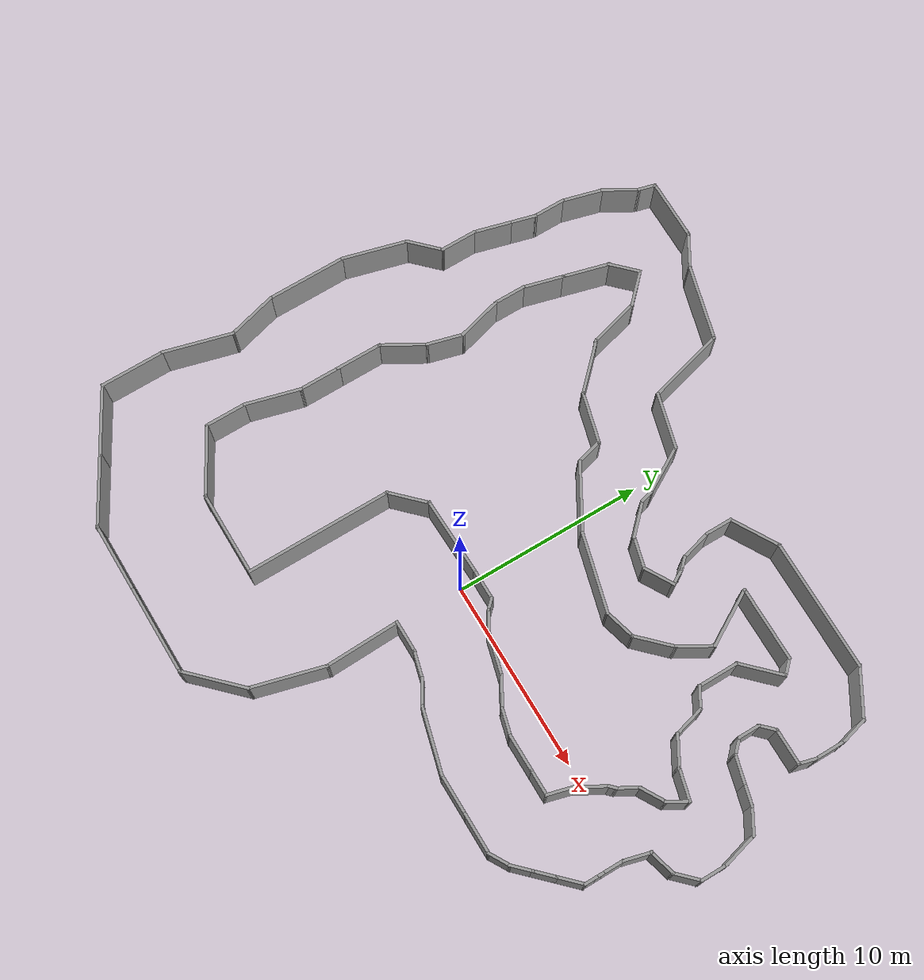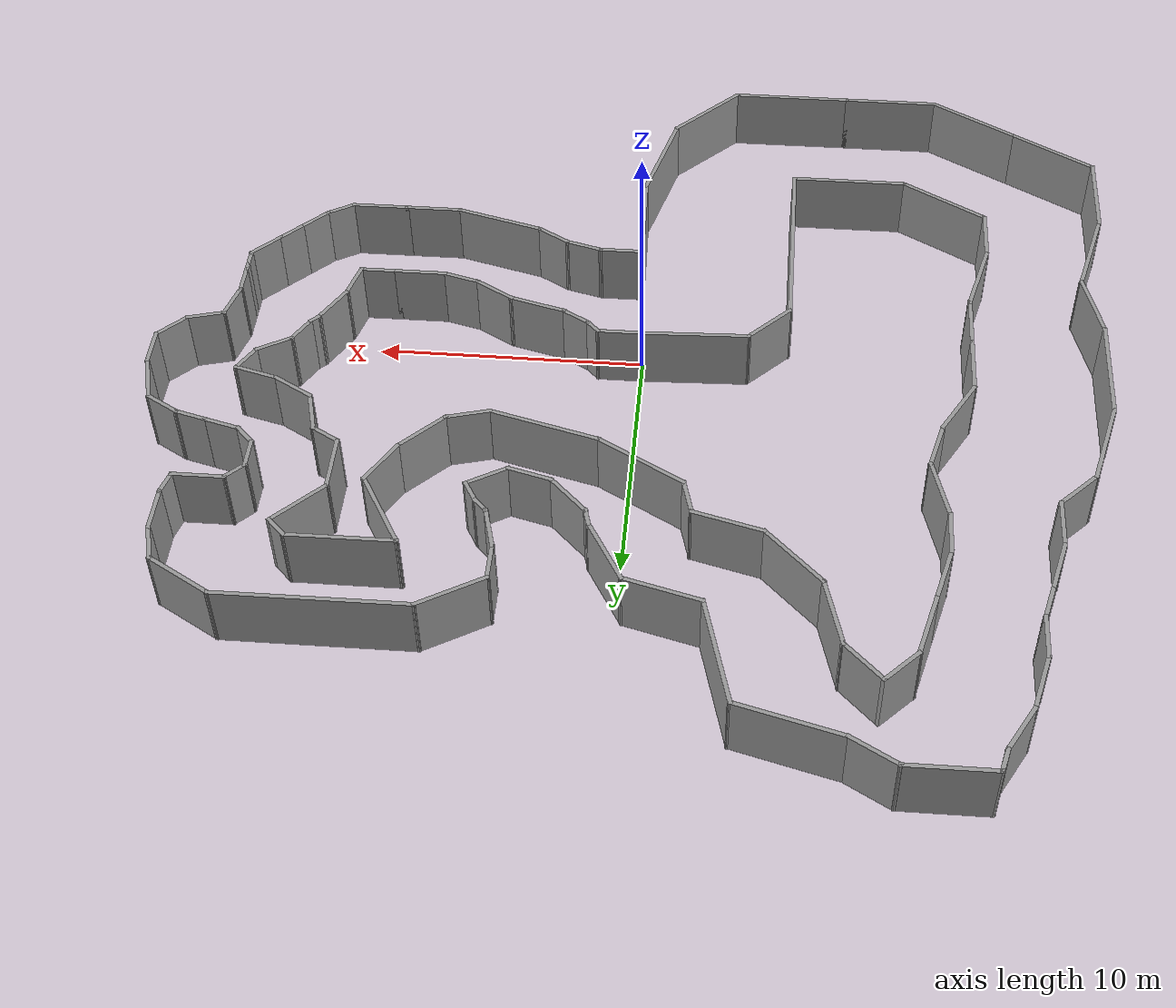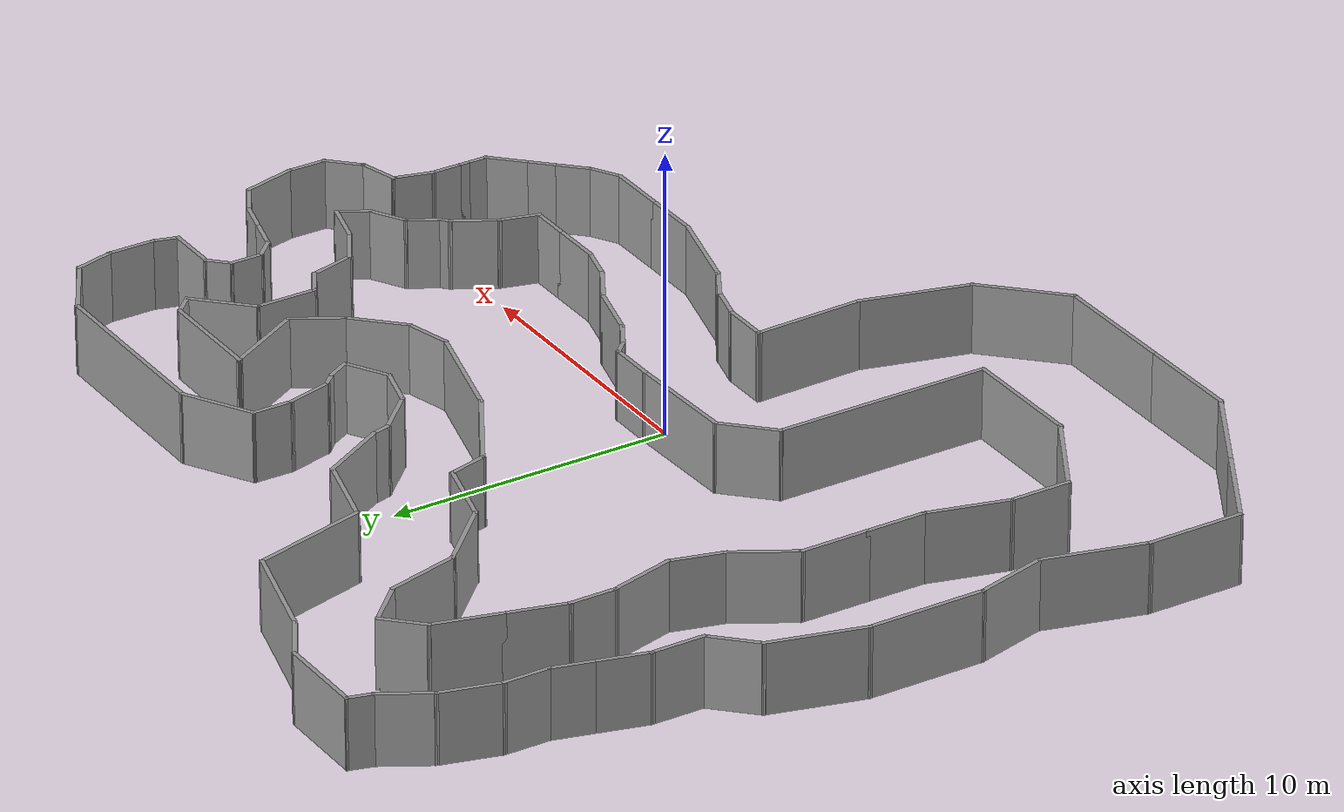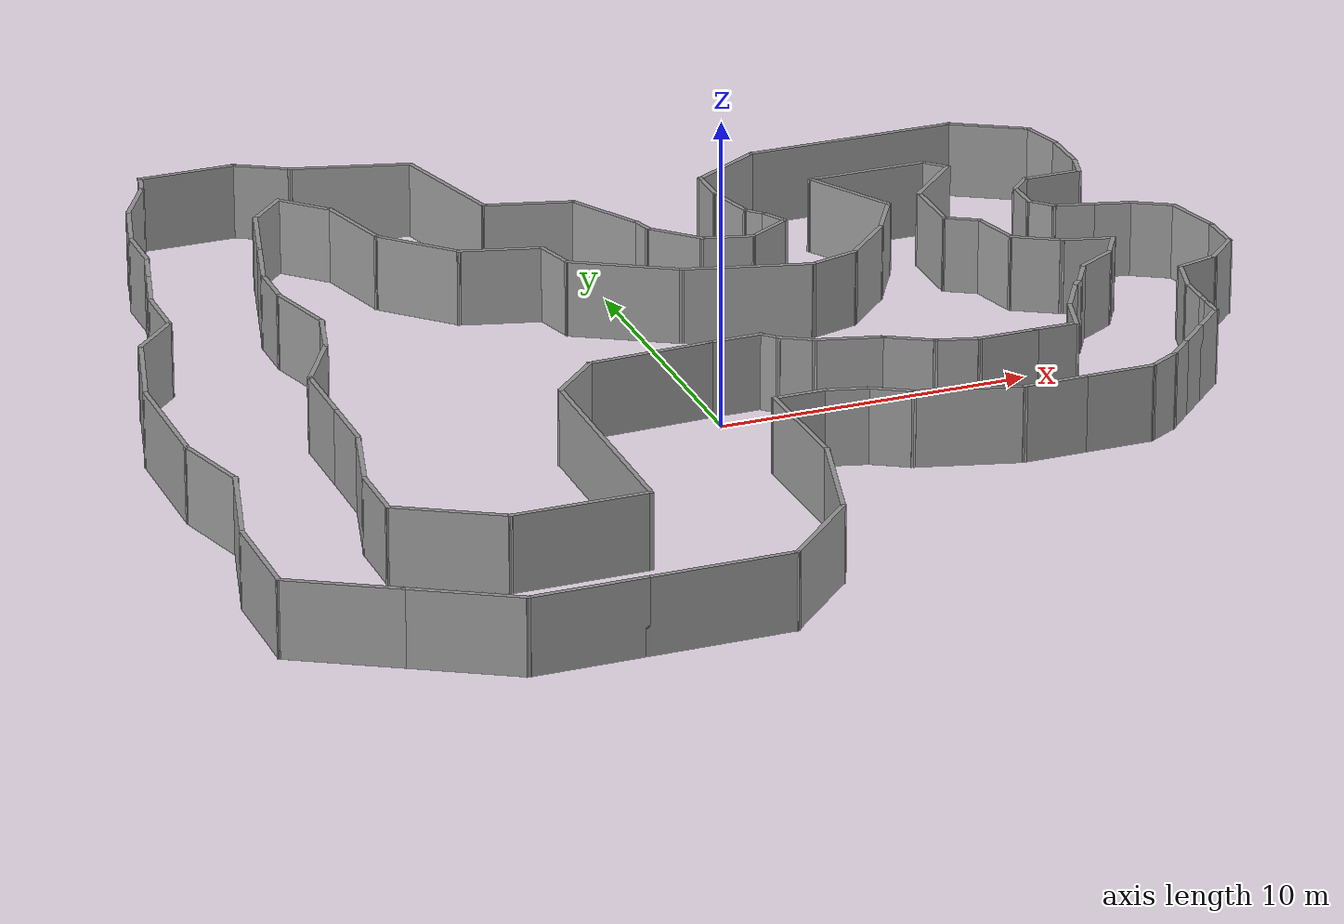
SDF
<?xml version='1.0'?>
<sdf version='1.7'>
  <model name='racetrackgap'>
    <pose>0.224585 2.63558 0 0 -0 0</pose>
    <link name='Wall_10'>
      <collision name='Wall_10_Collision'>
        <geometry>
          <box>
            <size>1.25 0.15 2.5</size>
          </box>
        </geometry>
        <pose>0 0 1.25 0 -0 0</pose>
      </collision>
      <visual name='Wall_10_Visual'>
        <pose>0 0 1.25 0 -0 0</pose>
        <geometry>
          <box>
            <size>1.25 0.15 2.5</size>
          </box>
        </geometry>
        <material>
          <script>
            <uri>file://media/materials/scripts/gazebo.material</uri>
            <name>Gazebo/Grey</name>
          </script>
          <ambient>1 1 1 1</ambient>
        </material>
        <meta>
          <layer>0</layer>
        </meta>
      </visual>
      <pose>12.9009 -7.28003 0 0 -0 0.785398</pose>
    </link>
    <link name='Wall_100'>
      <collision name='Wall_100_Collision'>
        <geometry>
          <box>
            <size>2.75 0.15 2.5</size>
          </box>
        </geometry>
        <pose>0 0 1.25 0 -0 0</pose>
      </collision>
      <visual name='Wall_100_Visual'>
        <pose>0 0 1.25 0 -0 0</pose>
        <geometry>
          <box>
            <size>2.75 0.15 2.5</size>
          </box>
        </geometry>
        <material>
          <script>
            <uri>file://media/materials/scripts/gazebo.material</uri>
            <name>Gazebo/Grey</name>
          </script>
          <ambient>1 1 1 1</ambient>
        </material>
        <meta>
          <layer>0</layer>
        </meta>
      </visual>
      <pose>-3.86239 6.95839 0 0 -0 2.87979</pose>
    </link>
    <link name='Wall_101'>
      <collision name='Wall_101_Collision'>
        <geometry>
          <box>
            <size>3 0.15 2.5</size>
          </box>
        </geometry>
        <pose>0 0 1.25 0 -0 0</pose>
      </collision>
      <visual name='Wall_101_Visual'>
        <pose>0 0 1.25 0 -0 0</pose>
        <geometry>
          <box>
            <size>3 0.15 2.5</size>
          </box>
        </geometry>
        <material>
          <script>
            <uri>file://media/materials/scripts/gazebo.material</uri>
            <name>Gazebo/Grey</name>
          </script>
          <ambient>1 1 1 1</ambient>
        </material>
        <meta>
          <layer>0</layer>
        </meta>
      </visual>
      <pose>-6.12573 8.30248 0 0 -0 2.35619</pose>
    </link>
    <link name='Wall_102'>
      <collision name='Wall_102_Collision'>
        <geometry>
          <box>
            <size>2.75 0.15 2.5</size>
          </box>
        </geometry>
        <pose>0 0 1.25 0 -0 0</pose>
      </collision>
      <visual name='Wall_102_Visual'>
        <pose>0 0 1.25 0 -0 0</pose>
        <geometry>
          <box>
            <size>2.75 0.15 2.5</size>
          </box>
        </geometry>
        <material>
          <script>
            <uri>file://media/materials/scripts/gazebo.material</uri>
            <name>Gazebo/Grey</name>
          </script>
          <ambient>1 1 1 1</ambient>
        </material>
        <meta>
          <layer>0</layer>
        </meta>
      </visual>
      <pose>-7.46982 10.5658 0 0 -0 1.8326</pose>
    </link>
    <link name='Wall_103'>
      <collision name='Wall_103_Collision'>
        <geometry>
          <box>
            <size>2 0.15 2.5</size>
          </box>
        </geometry>
        <pose>0 0 1.25 0 -0 0</pose>
      </collision>
      <visual name='Wall_103_Visual'>
        <pose>0 0 1.25 0 -0 0</pose>
        <geometry>
          <box>
            <size>2 0.15 2.5</size>
          </box>
        </geometry>
        <material>
          <script>
            <uri>file://media/materials/scripts/gazebo.material</uri>
            <name>Gazebo/Grey</name>
          </script>
          <ambient>1 1 1 1</ambient>
        </material>
        <meta>
          <layer>0</layer>
        </meta>
      </visual>
      <pose>-8.46036 12.4756 0 0 -0 2.35619</pose>
    </link>
    <link name='Wall_104'>
      <collision name='Wall_104_Collision'>
        <geometry>
          <box>
            <size>1.75 0.15 2.5</size>
          </box>
        </geometry>
        <pose>0 0 1.25 0 -0 0</pose>
      </collision>
      <visual name='Wall_104_Visual'>
        <pose>0 0 1.25 0 -0 0</pose>
        <geometry>
          <box>
            <size>1.75 0.15 2.5</size>
          </box>
        </geometry>
        <material>
          <script>
            <uri>file://media/materials/scripts/gazebo.material</uri>
            <name>Gazebo/Grey</name>
          </script>
          <ambient>1 1 1 1</ambient>
        </material>
        <meta>
          <layer>0</layer>
        </meta>
      </visual>
      <pose>-9.68012 12.564 0 0 -0 -2.35619</pose>
    </link>
    <link name='Wall_105'>
      <collision name='Wall_105_Collision'>
        <geometry>
          <box>
            <size>2.5 0.15 2.5</size>
          </box>
        </geometry>
        <pose>0 0 1.25 0 -0 0</pose>
      </collision>
      <visual name='Wall_105_Visual'>
        <pose>0 0 1.25 0 -0 0</pose>
        <geometry>
          <box>
            <size>2.5 0.15 2.5</size>
          </box>
        </geometry>
        <material>
          <script>
            <uri>file://media/materials/scripts/gazebo.material</uri>
            <name>Gazebo/Grey</name>
          </script>
          <ambient>1 1 1 1</ambient>
        </material>
        <meta>
          <layer>0</layer>
        </meta>
      </visual>
      <pose>-10.5499 10.8633 0 0 -0 -1.8326</pose>
    </link>
    <link name='Wall_106'>
      <collision name='Wall_106_Collision'>
        <geometry>
          <box>
            <size>2.25 0.15 2.5</size>
          </box>
        </geometry>
        <pose>0 0 1.25 0 -0 0</pose>
      </collision>
      <visual name='Wall_106_Visual'>
        <pose>0 0 1.25 0 -0 0</pose>
        <geometry>
          <box>
            <size>2.25 0.15 2.5</size>
          </box>
        </geometry>
        <material>
          <script>
            <uri>file://media/materials/scripts/gazebo.material</uri>
            <name>Gazebo/Grey</name>
          </script>
          <ambient>1 1 1 1</ambient>
        </material>
        <meta>
          <layer>0</layer>
        </meta>
      </visual>
      <pose>-11.1258 8.71414 0 0 -0 -1.8326</pose>
    </link>
    <link name='Wall_107'>
      <collision name='Wall_107_Collision'>
        <geometry>
          <box>
            <size>1.75 0.15 2.5</size>
          </box>
        </geometry>
        <pose>0 0 1.25 0 -0 0</pose>
      </collision>
      <visual name='Wall_107_Visual'>
        <pose>0 0 1.25 0 -0 0</pose>
        <geometry>
          <box>
            <size>1.75 0.15 2.5</size>
          </box>
        </geometry>
        <material>
          <script>
            <uri>file://media/materials/scripts/gazebo.material</uri>
            <name>Gazebo/Grey</name>
          </script>
          <ambient>1 1 1 1</ambient>
        </material>
        <meta>
          <layer>0</layer>
        </meta>
      </visual>
      <pose>-11.3975 6.89992 0 0 -0 -1.5708</pose>
    </link>
    <link name='Wall_108'>
      <collision name='Wall_108_Collision'>
        <geometry>
          <box>
            <size>2.5 0.15 2.5</size>
          </box>
        </geometry>
        <pose>0 0 1.25 0 -0 0</pose>
      </collision>
      <visual name='Wall_108_Visual'>
        <pose>0 0 1.25 0 -0 0</pose>
        <geometry>
          <box>
            <size>2.5 0.15 2.5</size>
          </box>
        </geometry>
        <material>
          <script>
            <uri>file://media/materials/scripts/gazebo.material</uri>
            <name>Gazebo/Grey</name>
          </script>
          <ambient>1 1 1 1</ambient>
        </material>
        <meta>
          <layer>0</layer>
        </meta>
      </visual>
      <pose>-11.0934 4.96496 0 0 -0 -1.309</pose>
    </link>
    <link name='Wall_109'>
      <collision name='Wall_109_Collision'>
        <geometry>
          <box>
            <size>2 0.15 2.5</size>
          </box>
        </geometry>
        <pose>0 0 1.25 0 -0 0</pose>
      </collision>
      <visual name='Wall_109_Visual'>
        <pose>0 0 1.25 0 -0 0</pose>
        <geometry>
          <box>
            <size>2 0.15 2.5</size>
          </box>
        </geometry>
        <material>
          <script>
            <uri>file://media/materials/scripts/gazebo.material</uri>
            <name>Gazebo/Grey</name>
          </script>
          <ambient>1 1 1 1</ambient>
        </material>
        <meta>
          <layer>0</layer>
        </meta>
      </visual>
      <pose>-11.0287 2.93651 0 0 -0 -1.8326</pose>
    </link>
    <link name='Wall_11'>
      <collision name='Wall_11_Collision'>
        <geometry>
          <box>
            <size>1.25 0.15 2.5</size>
          </box>
        </geometry>
        <pose>0 0 1.25 0 -0 0</pose>
      </collision>
      <visual name='Wall_11_Visual'>
        <pose>0 0 1.25 0 -0 0</pose>
        <geometry>
          <box>
            <size>1.25 0.15 2.5</size>
          </box>
        </geometry>
        <material>
          <script>
            <uri>file://media/materials/scripts/gazebo.material</uri>
            <name>Gazebo/Grey</name>
          </script>
          <ambient>1 1 1 1</ambient>
        </material>
        <meta>
          <layer>0</layer>
        </meta>
      </visual>
      <pose>13.6788 -6.50221 0 0 -0 0.785398</pose>
    </link>
    <link name='Wall_110'>
      <collision name='Wall_110_Collision'>
        <geometry>
          <box>
            <size>2.5 0.15 2.5</size>
          </box>
        </geometry>
        <pose>0 0 1.25 0 -0 0</pose>
      </collision>
      <visual name='Wall_110_Visual'>
        <pose>0 0 1.25 0 -0 0</pose>
        <geometry>
          <box>
            <size>2.5 0.15 2.5</size>
          </box>
        </geometry>
        <material>
          <script>
            <uri>file://media/materials/scripts/gazebo.material</uri>
            <name>Gazebo/Grey</name>
          </script>
          <ambient>1 1 1 1</ambient>
        </material>
        <meta>
          <layer>0</layer>
        </meta>
      </visual>
      <pose>-11.8556 1.02545 0 0 -0 -2.0944</pose>
    </link>
    <link name='Wall_111'>
      <collision name='Wall_111_Collision'>
        <geometry>
          <box>
            <size>2.5 0.15 2.5</size>
          </box>
        </geometry>
        <pose>0 0 1.25 0 -0 0</pose>
      </collision>
      <visual name='Wall_111_Visual'>
        <pose>0 0 1.25 0 -0 0</pose>
        <geometry>
          <box>
            <size>2.5 0.15 2.5</size>
          </box>
        </geometry>
        <material>
          <script>
            <uri>file://media/materials/scripts/gazebo.material</uri>
            <name>Gazebo/Grey</name>
          </script>
          <ambient>1 1 1 1</ambient>
        </material>
        <meta>
          <layer>0</layer>
        </meta>
      </visual>
      <pose>-12.4431 -1.16713 0 0 -0 -1.5708</pose>
    </link>
    <link name='Wall_112'>
      <collision name='Wall_112_Collision'>
        <geometry>
          <box>
            <size>2.25 0.15 2.5</size>
          </box>
        </geometry>
        <pose>0 0 1.25 0 -0 0</pose>
      </collision>
      <visual name='Wall_112_Visual'>
        <pose>0 0 1.25 0 -0 0</pose>
        <geometry>
          <box>
            <size>2.25 0.15 2.5</size>
          </box>
        </geometry>
        <material>
          <script>
            <uri>file://media/materials/scripts/gazebo.material</uri>
            <name>Gazebo/Grey</name>
          </script>
          <ambient>1 1 1 1</ambient>
        </material>
        <meta>
          <layer>0</layer>
        </meta>
      </visual>
      <pose>-12.4431 -3.39213 0 0 -0 -1.5708</pose>
    </link>
    <link name='Wall_113'>
      <collision name='Wall_113_Collision'>
        <geometry>
          <box>
            <size>3 0.15 2.5</size>
          </box>
        </geometry>
        <pose>0 0 1.25 0 -0 0</pose>
      </collision>
      <visual name='Wall_113_Visual'>
        <pose>0 0 1.25 0 -0 0</pose>
        <geometry>
          <box>
            <size>3 0.15 2.5</size>
          </box>
        </geometry>
        <material>
          <script>
            <uri>file://media/materials/scripts/gazebo.material</uri>
            <name>Gazebo/Grey</name>
          </script>
          <ambient>1 1 1 1</ambient>
        </material>
        <meta>
          <layer>0</layer>
        </meta>
      </visual>
      <pose>-12.812 -5.81857 0 0 -0 -1.8326</pose>
    </link>
    <link name='Wall_114'>
      <collision name='Wall_114_Collision'>
        <geometry>
          <box>
            <size>2.25 0.15 2.5</size>
          </box>
        </geometry>
        <pose>0 0 1.25 0 -0 0</pose>
      </collision>
      <visual name='Wall_114_Visual'>
        <pose>0 0 1.25 0 -0 0</pose>
        <geometry>
          <box>
            <size>2.25 0.15 2.5</size>
          </box>
        </geometry>
        <material>
          <script>
            <uri>file://media/materials/scripts/gazebo.material</uri>
            <name>Gazebo/Grey</name>
          </script>
          <ambient>1 1 1 1</ambient>
        </material>
        <meta>
          <layer>0</layer>
        </meta>
      </visual>
      <pose>-13.1808 -8.24502 0 0 -0 -1.5708</pose>
    </link>
    <link name='Wall_115'>
      <collision name='Wall_115_Collision'>
        <geometry>
          <box>
            <size>3.75 0.15 2.5</size>
          </box>
        </geometry>
        <pose>0 0 1.25 0 -0 0</pose>
      </collision>
      <visual name='Wall_115_Visual'>
        <pose>0 0 1.25 0 -0 0</pose>
        <geometry>
          <box>
            <size>3.75 0.15 2.5</size>
          </box>
        </geometry>
        <material>
          <script>
            <uri>file://media/materials/scripts/gazebo.material</uri>
            <name>Gazebo/Grey</name>
          </script>
          <ambient>1 1 1 1</ambient>
        </material>
        <meta>
          <layer>0</layer>
        </meta>
      </visual>
      <pose>-11.6219 -10.195 0 0 -0 -0.523599</pose>
    </link>
    <link name='Wall_116'>
      <collision name='Wall_116_Collision'>
        <geometry>
          <box>
            <size>4.5 0.15 2.5</size>
          </box>
        </geometry>
        <pose>0 0 1.25 0 -0 0</pose>
      </collision>
      <visual name='Wall_116_Visual'>
        <pose>0 0 1.25 0 -0 0</pose>
        <geometry>
          <box>
            <size>4.5 0.15 2.5</size>
          </box>
        </geometry>
        <material>
          <script>
            <uri>file://media/materials/scripts/gazebo.material</uri>
            <name>Gazebo/Grey</name>
          </script>
          <ambient>1 1 1 1</ambient>
        </material>
        <meta>
          <layer>0</layer>
        </meta>
      </visual>
      <pose>-7.88808 -11.095 0 0 -0 0</pose>
    </link>
    <link name='Wall_117'>
      <collision name='Wall_117_Collision'>
        <geometry>
          <box>
            <size>7.75 0.15 2.5</size>
          </box>
        </geometry>
        <pose>0 0 1.25 0 -0 0</pose>
      </collision>
      <visual name='Wall_117_Visual'>
        <pose>0 0 1.25 0 -0 0</pose>
        <geometry>
          <box>
            <size>7.75 0.15 2.5</size>
          </box>
        </geometry>
        <material>
          <script>
            <uri>file://media/materials/scripts/gazebo.material</uri>
            <name>Gazebo/Grey</name>
          </script>
          <ambient>1 1 1 1</ambient>
        </material>
        <meta>
          <layer>0</layer>
        </meta>
      </visual>
      <pose>-5.71308 -7.29502 0 0 -0 1.5708</pose>
    </link>
    <link name='Wall_118'>
      <collision name='Wall_118_Collision'>
        <geometry>
          <box>
            <size>2.25 0.15 2.5</size>
          </box>
        </geometry>
        <pose>0 0 1.25 0 -0 0</pose>
      </collision>
      <visual name='Wall_118_Visual'>
        <pose>0 0 1.25 0 -0 0</pose>
        <geometry>
          <box>
            <size>2.25 0.15 2.5</size>
          </box>
        </geometry>
        <material>
          <script>
            <uri>file://media/materials/scripts/gazebo.material</uri>
            <name>Gazebo/Grey</name>
          </script>
          <ambient>1 1 1 1</ambient>
        </material>
        <meta>
          <layer>0</layer>
        </meta>
      </visual>
      <pose>-4.97062 -2.75255 0 0 -0 0.785398</pose>
    </link>
    <link name='Wall_119'>
      <collision name='Wall_119_Collision'>
        <geometry>
          <box>
            <size>4.13259 0.15 2.5</size>
          </box>
        </geometry>
        <pose>0 0 1.25 0 -0 0</pose>
      </collision>
      <visual name='Wall_119_Visual'>
        <pose>0 0 1.25 0 -0 0</pose>
        <geometry>
          <box>
            <size>4.13259 0.15 2.5</size>
          </box>
        </geometry>
        <material>
          <script>
            <uri>file://media/materials/scripts/gazebo.material</uri>
            <name>Gazebo/Grey</name>
          </script>
          <ambient>1 1 1 1</ambient>
        </material>
        <meta>
          <layer>0</layer>
        </meta>
      </visual>
      <pose>-2.23793 -1.945 0 0 -0 0.032696</pose>
    </link>
    <link name='Wall_12'>
      <collision name='Wall_12_Collision'>
        <geometry>
          <box>
            <size>1.5 0.15 2.5</size>
          </box>
        </geometry>
        <pose>0 0 1.25 0 -0 0</pose>
      </collision>
      <visual name='Wall_12_Visual'>
        <pose>0 0 1.25 0 -0 0</pose>
        <geometry>
          <box>
            <size>1.5 0.15 2.5</size>
          </box>
        </geometry>
        <material>
          <script>
            <uri>file://media/materials/scripts/gazebo.material</uri>
            <name>Gazebo/Grey</name>
          </script>
          <ambient>1 1 1 1</ambient>
        </material>
        <meta>
          <layer>0</layer>
        </meta>
      </visual>
      <pose>14.545 -5.63601 0 0 -0 0.785398</pose>
    </link>
    <link name='Wall_13'>
      <collision name='Wall_13_Collision'>
        <geometry>
          <box>
            <size>0.75 0.15 2.5</size>
          </box>
        </geometry>
        <pose>0 0 1.25 0 -0 0</pose>
      </collision>
      <visual name='Wall_13_Visual'>
        <pose>0 0 1.25 0 -0 0</pose>
        <geometry>
          <box>
            <size>0.75 0.15 2.5</size>
          </box>
        </geometry>
        <material>
          <script>
            <uri>file://media/materials/scripts/gazebo.material</uri>
            <name>Gazebo/Grey</name>
          </script>
          <ambient>1 1 1 1</ambient>
        </material>
        <meta>
          <layer>0</layer>
        </meta>
      </visual>
      <pose>15.0223 -4.85871 0 0 -0 1.5708</pose>
    </link>
    <link name='Wall_14'>
      <collision name='Wall_14_Collision'>
        <geometry>
          <box>
            <size>0.5 0.15 2.5</size>
          </box>
        </geometry>
        <pose>0 0 1.25 0 -0 0</pose>
      </collision>
      <visual name='Wall_14_Visual'>
        <pose>0 0 1.25 0 -0 0</pose>
        <geometry>
          <box>
            <size>0.5 0.15 2.5</size>
          </box>
        </geometry>
        <material>
          <script>
            <uri>file://media/materials/scripts/gazebo.material</uri>
            <name>Gazebo/Grey</name>
          </script>
          <ambient>1 1 1 1</ambient>
        </material>
        <meta>
          <layer>0</layer>
        </meta>
      </visual>
      <pose>15.0223 -4.38371 0 0 -0 1.5708</pose>
    </link>
    <link name='Wall_15'>
      <collision name='Wall_15_Collision'>
        <geometry>
          <box>
            <size>1.25 0.15 2.5</size>
          </box>
        </geometry>
        <pose>0 0 1.25 0 -0 0</pose>
      </collision>
      <visual name='Wall_15_Visual'>
        <pose>0 0 1.25 0 -0 0</pose>
        <geometry>
          <box>
            <size>1.25 0.15 2.5</size>
          </box>
        </geometry>
        <material>
          <script>
            <uri>file://media/materials/scripts/gazebo.material</uri>
            <name>Gazebo/Grey</name>
          </script>
          <ambient>1 1 1 1</ambient>
        </material>
        <meta>
          <layer>0</layer>
        </meta>
      </visual>
      <pose>15.0223 -3.65871 0 0 -0 1.5708</pose>
    </link>
    <link name='Wall_16'>
      <collision name='Wall_16_Collision'>
        <geometry>
          <box>
            <size>1.5 0.15 2.5</size>
          </box>
        </geometry>
        <pose>0 0 1.25 0 -0 0</pose>
      </collision>
      <visual name='Wall_16_Visual'>
        <pose>0 0 1.25 0 -0 0</pose>
        <geometry>
          <box>
            <size>1.5 0.15 2.5</size>
          </box>
        </geometry>
        <material>
          <script>
            <uri>file://media/materials/scripts/gazebo.material</uri>
            <name>Gazebo/Grey</name>
          </script>
          <ambient>1 1 1 1</ambient>
        </material>
        <meta>
          <layer>0</layer>
        </meta>
      </visual>
      <pose>15.197 -2.45671 0 0 -0 1.309</pose>
    </link>
    <link name='Wall_17'>
      <collision name='Wall_17_Collision'>
        <geometry>
          <box>
            <size>1.5 0.15 2.5</size>
          </box>
        </geometry>
        <pose>0 0 1.25 0 -0 0</pose>
      </collision>
      <visual name='Wall_17_Visual'>
        <pose>0 0 1.25 0 -0 0</pose>
        <geometry>
          <box>
            <size>1.5 0.15 2.5</size>
          </box>
        </geometry>
        <material>
          <script>
            <uri>file://media/materials/scripts/gazebo.material</uri>
            <name>Gazebo/Grey</name>
          </script>
          <ambient>1 1 1 1</ambient>
        </material>
        <meta>
          <layer>0</layer>
        </meta>
      </visual>
      <pose>16.0237 -1.63001 0 0 -0 0.261799</pose>
    </link>
    <link name='Wall_18'>
      <collision name='Wall_18_Collision'>
        <geometry>
          <box>
            <size>1.5 0.15 2.5</size>
          </box>
        </geometry>
        <pose>0 0 1.25 0 -0 0</pose>
      </collision>
      <visual name='Wall_18_Visual'>
        <pose>0 0 1.25 0 -0 0</pose>
        <geometry>
          <box>
            <size>1.5 0.15 2.5</size>
          </box>
        </geometry>
        <material>
          <script>
            <uri>file://media/materials/scripts/gazebo.material</uri>
            <name>Gazebo/Grey</name>
          </script>
          <ambient>1 1 1 1</ambient>
        </material>
        <meta>
          <layer>0</layer>
        </meta>
      </visual>
      <pose>17.153 -0.978009 0 0 -0 0.785398</pose>
    </link>
    <link name='Wall_19'>
      <collision name='Wall_19_Collision'>
        <geometry>
          <box>
            <size>1.5 0.15 2.5</size>
          </box>
        </geometry>
        <pose>0 0 1.25 0 -0 0</pose>
      </collision>
      <visual name='Wall_19_Visual'>
        <pose>0 0 1.25 0 -0 0</pose>
        <geometry>
          <box>
            <size>1.5 0.15 2.5</size>
          </box>
        </geometry>
        <material>
          <script>
            <uri>file://media/materials/scripts/gazebo.material</uri>
            <name>Gazebo/Grey</name>
          </script>
          <ambient>1 1 1 1</ambient>
        </material>
        <meta>
          <layer>0</layer>
        </meta>
      </visual>
      <pose>17.6303 0.174289 0 0 -0 1.5708</pose>
    </link>
    <link name='Wall_20'>
      <collision name='Wall_20_Collision'>
        <geometry>
          <box>
            <size>2 0.15 2.5</size>
          </box>
        </geometry>
        <pose>0 0 1.25 0 -0 0</pose>
      </collision>
      <visual name='Wall_20_Visual'>
        <pose>0 0 1.25 0 -0 0</pose>
        <geometry>
          <box>
            <size>2 0.15 2.5</size>
          </box>
        </geometry>
        <material>
          <script>
            <uri>file://media/materials/scripts/gazebo.material</uri>
            <name>Gazebo/Grey</name>
          </script>
          <ambient>1 1 1 1</ambient>
        </material>
        <meta>
          <layer>0</layer>
        </meta>
      </visual>
      <pose>17.3909 1.74277 0 0 -0 1.8326</pose>
    </link>
    <link name='Wall_21'>
      <collision name='Wall_21_Collision'>
        <geometry>
          <box>
            <size>1.5 0.15 2.5</size>
          </box>
        </geometry>
        <pose>0 0 1.25 0 -0 0</pose>
      </collision>
      <visual name='Wall_21_Visual'>
        <pose>0 0 1.25 0 -0 0</pose>
        <geometry>
          <box>
            <size>1.5 0.15 2.5</size>
          </box>
        </geometry>
        <material>
          <script>
            <uri>file://media/materials/scripts/gazebo.material</uri>
            <name>Gazebo/Grey</name>
          </script>
          <ambient>1 1 1 1</ambient>
        </material>
        <meta>
          <layer>0</layer>
        </meta>
      </visual>
      <pose>16.5669 2.97375 0 0 -0 2.61799</pose>
    </link>
    <link name='Wall_22'>
      <collision name='Wall_22_Collision'>
        <geometry>
          <box>
            <size>1.25 0.15 2.5</size>
          </box>
        </geometry>
        <pose>0 0 1.25 0 -0 0</pose>
      </collision>
      <visual name='Wall_22_Visual'>
        <pose>0 0 1.25 0 -0 0</pose>
        <geometry>
          <box>
            <size>1.25 0.15 2.5</size>
          </box>
        </geometry>
        <material>
          <script>
            <uri>file://media/materials/scripts/gazebo.material</uri>
            <name>Gazebo/Grey</name>
          </script>
          <ambient>1 1 1 1</ambient>
        </material>
        <meta>
          <layer>0</layer>
        </meta>
      </visual>
      <pose>15.4511 3.4536 0 0 -0 2.87979</pose>
    </link>
    <link name='Wall_23'>
      <collision name='Wall_23_Collision'>
        <geometry>
          <box>
            <size>1.5 0.15 2.5</size>
          </box>
        </geometry>
        <pose>0 0 1.25 0 -0 0</pose>
      </collision>
      <visual name='Wall_23_Visual'>
        <pose>0 0 1.25 0 -0 0</pose>
        <geometry>
          <box>
            <size>1.5 0.15 2.5</size>
          </box>
        </geometry>
        <material>
          <script>
            <uri>file://media/materials/scripts/gazebo.material</uri>
            <name>Gazebo/Grey</name>
          </script>
          <ambient>1 1 1 1</ambient>
        </material>
        <meta>
          <layer>0</layer>
        </meta>
      </visual>
      <pose>14.2678 3.77066 0 0 -0 2.87979</pose>
    </link>
    <link name='Wall_24'>
      <collision name='Wall_24_Collision'>
        <geometry>
          <box>
            <size>1 0.15 2.5</size>
          </box>
        </geometry>
        <pose>0 0 1.25 0 -0 0</pose>
      </collision>
      <visual name='Wall_24_Visual'>
        <pose>0 0 1.25 0 -0 0</pose>
        <geometry>
          <box>
            <size>1 0.15 2.5</size>
          </box>
        </geometry>
        <material>
          <script>
            <uri>file://media/materials/scripts/gazebo.material</uri>
            <name>Gazebo/Grey</name>
          </script>
          <ambient>1 1 1 1</ambient>
        </material>
        <meta>
          <layer>0</layer>
        </meta>
      </visual>
      <pose>13.3153 4.24588 0 0 -0 2.35619</pose>
    </link>
    <link name='Wall_27'>
      <collision name='Wall_27_Collision'>
        <geometry>
          <box>
            <size>1.25 0.15 2.5</size>
          </box>
        </geometry>
        <pose>0 0 1.25 0 -0 0</pose>
      </collision>
      <visual name='Wall_27_Visual'>
        <pose>0 0 1.25 0 -0 0</pose>
        <geometry>
          <box>
            <size>1.25 0.15 2.5</size>
          </box>
        </geometry>
        <material>
          <script>
            <uri>file://media/materials/scripts/gazebo.material</uri>
            <name>Gazebo/Grey</name>
          </script>
          <ambient>1 1 1 1</ambient>
        </material>
        <meta>
          <layer>0</layer>
        </meta>
      </visual>
      <pose>13.0148 5.0964 0 0 -0 1.5708</pose>
    </link>
    <link name='Wall_28'>
      <collision name='Wall_28_Collision'>
        <geometry>
          <box>
            <size>1 0.15 2.5</size>
          </box>
        </geometry>
        <pose>0 0 1.25 0 -0 0</pose>
      </collision>
      <visual name='Wall_28_Visual'>
        <pose>0 0 1.25 0 -0 0</pose>
        <geometry>
          <box>
            <size>1 0.15 2.5</size>
          </box>
        </geometry>
        <material>
          <script>
            <uri>file://media/materials/scripts/gazebo.material</uri>
            <name>Gazebo/Grey</name>
          </script>
          <ambient>1 1 1 1</ambient>
        </material>
        <meta>
          <layer>0</layer>
        </meta>
      </visual>
      <pose>13.3153 5.94692 0 0 -0 0.785398</pose>
    </link>
    <link name='Wall_29'>
      <collision name='Wall_29_Collision'>
        <geometry>
          <box>
            <size>2 0.15 2.5</size>
          </box>
        </geometry>
        <pose>0 0 1.25 0 -0 0</pose>
      </collision>
      <visual name='Wall_29_Visual'>
        <pose>0 0 1.25 0 -0 0</pose>
        <geometry>
          <box>
            <size>2 0.15 2.5</size>
          </box>
        </geometry>
        <material>
          <script>
            <uri>file://media/materials/scripts/gazebo.material</uri>
            <name>Gazebo/Grey</name>
          </script>
          <ambient>1 1 1 1</ambient>
        </material>
        <meta>
          <layer>0</layer>
        </meta>
      </visual>
      <pose>14.5408 6.24744 0 0 -0 0</pose>
    </link>
    <link name='Wall_3'>
      <collision name='Wall_3_Collision'>
        <geometry>
          <box>
            <size>1.75 0.15 2.5</size>
          </box>
        </geometry>
        <pose>0 0 1.25 0 -0 0</pose>
      </collision>
      <visual name='Wall_3_Visual'>
        <pose>0 0 1.25 0 -0 0</pose>
        <geometry>
          <box>
            <size>1.75 0.15 2.5</size>
          </box>
        </geometry>
        <material>
          <script>
            <uri>file://media/materials/scripts/gazebo.material</uri>
            <name>Gazebo/Grey</name>
          </script>
          <ambient>1 1 1 1</ambient>
        </material>
        <meta>
          <layer>0</layer>
        </meta>
      </visual>
      <pose>0.850427 -6.32749 0 0 -0 0</pose>
    </link>
    <link name='Wall_30'>
      <collision name='Wall_30_Collision'>
        <geometry>
          <box>
            <size>1 0.15 2.5</size>
          </box>
        </geometry>
        <pose>0 0 1.25 0 -0 0</pose>
      </collision>
      <visual name='Wall_30_Visual'>
        <pose>0 0 1.25 0 -0 0</pose>
        <geometry>
          <box>
            <size>1 0.15 2.5</size>
          </box>
        </geometry>
        <material>
          <script>
            <uri>file://media/materials/scripts/gazebo.material</uri>
            <name>Gazebo/Grey</name>
          </script>
          <ambient>1 1 1 1</ambient>
        </material>
        <meta>
          <layer>0</layer>
        </meta>
      </visual>
      <pose>15.5758 6.65796 0 0 -0 1.309</pose>
    </link>
    <link name='Wall_31'>
      <collision name='Wall_31_Collision'>
        <geometry>
          <box>
            <size>1.75 0.15 2.5</size>
          </box>
        </geometry>
        <pose>0 0 1.25 0 -0 0</pose>
      </collision>
      <visual name='Wall_31_Visual'>
        <pose>0 0 1.25 0 -0 0</pose>
        <geometry>
          <box>
            <size>1.75 0.15 2.5</size>
          </box>
        </geometry>
        <material>
          <script>
            <uri>file://media/materials/scripts/gazebo.material</uri>
            <name>Gazebo/Grey</name>
          </script>
          <ambient>1 1 1 1</ambient>
        </material>
        <meta>
          <layer>0</layer>
        </meta>
      </visual>
      <pose>15.6858 7.86848 0 0 -0 1.5708</pose>
    </link>
    <link name='Wall_32'>
      <collision name='Wall_32_Collision'>
        <geometry>
          <box>
            <size>1.5 0.15 2.5</size>
          </box>
        </geometry>
        <pose>0 0 1.25 0 -0 0</pose>
      </collision>
      <visual name='Wall_32_Visual'>
        <pose>0 0 1.25 0 -0 0</pose>
        <geometry>
          <box>
            <size>1.5 0.15 2.5</size>
          </box>
        </geometry>
        <material>
          <script>
            <uri>file://media/materials/scripts/gazebo.material</uri>
            <name>Gazebo/Grey</name>
          </script>
          <ambient>1 1 1 1</ambient>
        </material>
        <meta>
          <layer>0</layer>
        </meta>
      </visual>
      <pose>15.5111 9.32048 0 0 -0 1.8326</pose>
    </link>
    <link name='Wall_33'>
      <collision name='Wall_33_Collision'>
        <geometry>
          <box>
            <size>2.75 0.15 2.5</size>
          </box>
        </geometry>
        <pose>0 0 1.25 0 -0 0</pose>
      </collision>
      <visual name='Wall_33_Visual'>
        <pose>0 0 1.25 0 -0 0</pose>
        <geometry>
          <box>
            <size>2.75 0.15 2.5</size>
          </box>
        </geometry>
        <material>
          <script>
            <uri>file://media/materials/scripts/gazebo.material</uri>
            <name>Gazebo/Grey</name>
          </script>
          <ambient>1 1 1 1</ambient>
        </material>
        <meta>
          <layer>0</layer>
        </meta>
      </visual>
      <pose>14.2106 10.6225 0 0 -0 2.61799</pose>
    </link>
    <link name='Wall_34'>
      <collision name='Wall_34_Collision'>
        <geometry>
          <box>
            <size>7 0.15 2.5</size>
          </box>
        </geometry>
        <pose>0 0 1.25 0 -0 0</pose>
      </collision>
      <visual name='Wall_34_Visual'>
        <pose>0 0 1.25 0 -0 0</pose>
        <geometry>
          <box>
            <size>7 0.15 2.5</size>
          </box>
        </geometry>
        <material>
          <script>
            <uri>file://media/materials/scripts/gazebo.material</uri>
            <name>Gazebo/Grey</name>
          </script>
          <ambient>1 1 1 1</ambient>
        </material>
        <meta>
          <layer>0</layer>
        </meta>
      </visual>
      <pose>9.65973 11.2725 0 0 -0 3.14159</pose>
    </link>
    <link name='Wall_35'>
      <collision name='Wall_35_Collision'>
        <geometry>
          <box>
            <size>2.75 0.15 2.5</size>
          </box>
        </geometry>
        <pose>0 0 1.25 0 -0 0</pose>
      </collision>
      <visual name='Wall_35_Visual'>
        <pose>0 0 1.25 0 -0 0</pose>
        <geometry>
          <box>
            <size>2.75 0.15 2.5</size>
          </box>
        </geometry>
        <material>
          <script>
            <uri>file://media/materials/scripts/gazebo.material</uri>
            <name>Gazebo/Grey</name>
          </script>
          <ambient>1 1 1 1</ambient>
        </material>
        <meta>
          <layer>0</layer>
        </meta>
      </visual>
      <pose>5.10889 10.6225 0 0 -0 -2.61799</pose>
    </link>
    <link name='Wall_36'>
      <collision name='Wall_36_Collision'>
        <geometry>
          <box>
            <size>1.5 0.15 2.5</size>
          </box>
        </geometry>
        <pose>0 0 1.25 0 -0 0</pose>
      </collision>
      <visual name='Wall_36_Visual'>
        <pose>0 0 1.25 0 -0 0</pose>
        <geometry>
          <box>
            <size>1.5 0.15 2.5</size>
          </box>
        </geometry>
        <material>
          <script>
            <uri>file://media/materials/scripts/gazebo.material</uri>
            <name>Gazebo/Grey</name>
          </script>
          <ambient>1 1 1 1</ambient>
        </material>
        <meta>
          <layer>0</layer>
        </meta>
      </visual>
      <pose>3.98306 9.29748 0 0 -0 -1.5708</pose>
    </link>
    <link name='Wall_37'>
      <collision name='Wall_37_Collision'>
        <geometry>
          <box>
            <size>1.75 0.15 2.5</size>
          </box>
        </geometry>
        <pose>0 0 1.25 0 -0 0</pose>
      </collision>
      <visual name='Wall_37_Visual'>
        <pose>0 0 1.25 0 -0 0</pose>
        <geometry>
          <box>
            <size>1.75 0.15 2.5</size>
          </box>
        </geometry>
        <material>
          <script>
            <uri>file://media/materials/scripts/gazebo.material</uri>
            <name>Gazebo/Grey</name>
          </script>
          <ambient>1 1 1 1</ambient>
        </material>
        <meta>
          <layer>0</layer>
        </meta>
      </visual>
      <pose>4.19011 7.84974 0 0 -0 -1.309</pose>
    </link>
    <link name='Wall_38'>
      <collision name='Wall_38_Collision'>
        <geometry>
          <box>
            <size>0.75 0.15 2.5</size>
          </box>
        </geometry>
        <pose>0 0 1.25 0 -0 0</pose>
      </collision>
      <visual name='Wall_38_Visual'>
        <pose>0 0 1.25 0 -0 0</pose>
        <geometry>
          <box>
            <size>0.75 0.15 2.5</size>
          </box>
        </geometry>
        <material>
          <script>
            <uri>file://media/materials/scripts/gazebo.material</uri>
            <name>Gazebo/Grey</name>
          </script>
          <ambient>1 1 1 1</ambient>
        </material>
        <meta>
          <layer>0</layer>
        </meta>
      </visual>
      <pose>4.6093 6.86486 0 0 -0 -0.785398</pose>
    </link>
    <link name='Wall_39'>
      <collision name='Wall_39_Collision'>
        <geometry>
          <box>
            <size>1 0.15 2.5</size>
          </box>
        </geometry>
        <pose>0 0 1.25 0 -0 0</pose>
      </collision>
      <visual name='Wall_39_Visual'>
        <pose>0 0 1.25 0 -0 0</pose>
        <geometry>
          <box>
            <size>1 0.15 2.5</size>
          </box>
        </geometry>
        <material>
          <script>
            <uri>file://media/materials/scripts/gazebo.material</uri>
            <name>Gazebo/Grey</name>
          </script>
          <ambient>1 1 1 1</ambient>
        </material>
        <meta>
          <layer>0</layer>
        </meta>
      </visual>
      <pose>5.03393 6.28467 0 0 -0 -1.0472</pose>
    </link>
    <link name='Wall_4'>
      <collision name='Wall_4_Collision'>
        <geometry>
          <box>
            <size>1.5 0.15 2.5</size>
          </box>
        </geometry>
        <pose>0 0 1.25 0 -0 0</pose>
      </collision>
      <visual name='Wall_4_Visual'>
        <pose>0 0 1.25 0 -0 0</pose>
        <geometry>
          <box>
            <size>1.5 0.15 2.5</size>
          </box>
        </geometry>
        <material>
          <script>
            <uri>file://media/materials/scripts/gazebo.material</uri>
            <name>Gazebo/Grey</name>
          </script>
          <ambient>1 1 1 1</ambient>
        </material>
        <meta>
          <layer>0</layer>
        </meta>
      </visual>
      <pose>2.30243 -6.50219 0 0 -0 -0.261799</pose>
    </link>
    <link name='Wall_40'>
      <collision name='Wall_40_Collision'>
        <geometry>
          <box>
            <size>1.75 0.15 2.5</size>
          </box>
        </geometry>
        <pose>0 0 1.25 0 -0 0</pose>
      </collision>
      <visual name='Wall_40_Visual'>
        <pose>0 0 1.25 0 -0 0</pose>
        <geometry>
          <box>
            <size>1.75 0.15 2.5</size>
          </box>
        </geometry>
        <material>
          <script>
            <uri>file://media/materials/scripts/gazebo.material</uri>
            <name>Gazebo/Grey</name>
          </script>
          <ambient>1 1 1 1</ambient>
        </material>
        <meta>
          <layer>0</layer>
        </meta>
      </visual>
      <pose>4.55361 5.51661 0 0 -0 -2.61799</pose>
    </link>
    <link name='Wall_41'>
      <collision name='Wall_41_Collision'>
        <geometry>
          <box>
            <size>1.75 0.15 2.5</size>
          </box>
        </geometry>
        <pose>0 0 1.25 0 -0 0</pose>
      </collision>
      <visual name='Wall_41_Visual'>
        <pose>0 0 1.25 0 -0 0</pose>
        <geometry>
          <box>
            <size>1.75 0.15 2.5</size>
          </box>
        </geometry>
        <material>
          <script>
            <uri>file://media/materials/scripts/gazebo.material</uri>
            <name>Gazebo/Grey</name>
          </script>
          <ambient>1 1 1 1</ambient>
        </material>
        <meta>
          <layer>0</layer>
        </meta>
      </visual>
      <pose>3.08805 5.32367 0 0 -0 2.87979</pose>
    </link>
    <link name='Wall_42'>
      <collision name='Wall_42_Collision'>
        <geometry>
          <box>
            <size>2 0.15 2.5</size>
          </box>
        </geometry>
        <pose>0 0 1.25 0 -0 0</pose>
      </collision>
      <visual name='Wall_42_Visual'>
        <pose>0 0 1.25 0 -0 0</pose>
        <geometry>
          <box>
            <size>2 0.15 2.5</size>
          </box>
        </geometry>
        <material>
          <script>
            <uri>file://media/materials/scripts/gazebo.material</uri>
            <name>Gazebo/Grey</name>
          </script>
          <ambient>1 1 1 1</ambient>
        </material>
        <meta>
          <layer>0</layer>
        </meta>
      </visual>
      <pose>1.66124 6.18479 0 0 -0 2.35619</pose>
    </link>
    <link name='Wall_43'>
      <collision name='Wall_43_Collision'>
        <geometry>
          <box>
            <size>0.75 0.15 2.5</size>
          </box>
        </geometry>
        <pose>0 0 1.25 0 -0 0</pose>
      </collision>
      <visual name='Wall_43_Visual'>
        <pose>0 0 1.25 0 -0 0</pose>
        <geometry>
          <box>
            <size>0.75 0.15 2.5</size>
          </box>
        </geometry>
        <material>
          <script>
            <uri>file://media/materials/scripts/gazebo.material</uri>
            <name>Gazebo/Grey</name>
          </script>
          <ambient>1 1 1 1</ambient>
        </material>
        <meta>
          <layer>0</layer>
        </meta>
      </visual>
      <pose>0.929519 7.12864 0 0 -0 1.8326</pose>
    </link>
    <link name='Wall_44'>
      <collision name='Wall_44_Collision'>
        <geometry>
          <box>
            <size>2.75 0.15 2.5</size>
          </box>
        </geometry>
        <pose>0 0 1.25 0 -0 0</pose>
      </collision>
      <visual name='Wall_44_Visual'>
        <pose>0 0 1.25 0 -0 0</pose>
        <geometry>
          <box>
            <size>2.75 0.15 2.5</size>
          </box>
        </geometry>
        <material>
          <script>
            <uri>file://media/materials/scripts/gazebo.material</uri>
            <name>Gazebo/Grey</name>
          </script>
          <ambient>1 1 1 1</ambient>
        </material>
        <meta>
          <layer>0</layer>
        </meta>
      </visual>
      <pose>0.201873 8.54426 0 0 -0 2.0944</pose>
    </link>
    <link name='Wall_45'>
      <collision name='Wall_45_Collision'>
        <geometry>
          <box>
            <size>3 0.15 2.5</size>
          </box>
        </geometry>
        <pose>0 0 1.25 0 -0 0</pose>
      </collision>
      <visual name='Wall_45_Visual'>
        <pose>0 0 1.25 0 -0 0</pose>
        <geometry>
          <box>
            <size>3 0.15 2.5</size>
          </box>
        </geometry>
        <material>
          <script>
            <uri>file://media/materials/scripts/gazebo.material</uri>
            <name>Gazebo/Grey</name>
          </script>
          <ambient>1 1 1 1</ambient>
        </material>
        <meta>
          <layer>0</layer>
        </meta>
      </visual>
      <pose>-1.82457 10.0389 0 0 -0 2.87979</pose>
    </link>
    <link name='Wall_46'>
      <collision name='Wall_46_Collision'>
        <geometry>
          <box>
            <size>4.25 0.15 2.5</size>
          </box>
        </geometry>
        <pose>0 0 1.25 0 -0 0</pose>
      </collision>
      <visual name='Wall_46_Visual'>
        <pose>0 0 1.25 0 -0 0</pose>
        <geometry>
          <box>
            <size>4.25 0.15 2.5</size>
          </box>
        </geometry>
        <material>
          <script>
            <uri>file://media/materials/scripts/gazebo.material</uri>
            <name>Gazebo/Grey</name>
          </script>
          <ambient>1 1 1 1</ambient>
        </material>
        <meta>
          <layer>0</layer>
        </meta>
      </visual>
      <pose>-3.73159 12.3879 0 0 -0 1.8326</pose>
    </link>
    <link name='Wall_47'>
      <collision name='Wall_47_Collision'>
        <geometry>
          <box>
            <size>4 0.15 2.5</size>
          </box>
        </geometry>
        <pose>0 0 1.25 0 -0 0</pose>
      </collision>
      <visual name='Wall_47_Visual'>
        <pose>0 0 1.25 0 -0 0</pose>
        <geometry>
          <box>
            <size>4 0.15 2.5</size>
          </box>
        </geometry>
        <material>
          <script>
            <uri>file://media/materials/scripts/gazebo.material</uri>
            <name>Gazebo/Grey</name>
          </script>
          <ambient>1 1 1 1</ambient>
        </material>
        <meta>
          <layer>0</layer>
        </meta>
      </visual>
      <pose>-6.12158 14.8662 0 0 -0 2.87979</pose>
    </link>
    <link name='Wall_48'>
      <collision name='Wall_48_Collision'>
        <geometry>
          <box>
            <size>2 0.15 2.5</size>
          </box>
        </geometry>
        <pose>0 0 1.25 0 -0 0</pose>
      </collision>
      <visual name='Wall_48_Visual'>
        <pose>0 0 1.25 0 -0 0</pose>
        <geometry>
          <box>
            <size>2 0.15 2.5</size>
          </box>
        </geometry>
        <material>
          <script>
            <uri>file://media/materials/scripts/gazebo.material</uri>
            <name>Gazebo/Grey</name>
          </script>
          <ambient>1 1 1 1</ambient>
        </material>
        <meta>
          <layer>0</layer>
        </meta>
      </visual>
      <pose>-8.78206 15.827 0 0 -0 2.61799</pose>
    </link>
    <link name='Wall_49'>
      <collision name='Wall_49_Collision'>
        <geometry>
          <box>
            <size>3.25 0.15 2.5</size>
          </box>
        </geometry>
        <pose>0 0 1.25 0 -0 0</pose>
      </collision>
      <visual name='Wall_49_Visual'>
        <pose>0 0 1.25 0 -0 0</pose>
        <geometry>
          <box>
            <size>3.25 0.15 2.5</size>
          </box>
        </geometry>
        <material>
          <script>
            <uri>file://media/materials/scripts/gazebo.material</uri>
            <name>Gazebo/Grey</name>
          </script>
          <ambient>1 1 1 1</ambient>
        </material>
        <meta>
          <layer>0</layer>
        </meta>
      </visual>
      <pose>-11.1331 16.2895 0 0 -0 3.14159</pose>
    </link>
    <link name='Wall_5'>
      <collision name='Wall_5_Collision'>
        <geometry>
          <box>
            <size>1.5 0.15 2.5</size>
          </box>
        </geometry>
        <pose>0 0 1.25 0 -0 0</pose>
      </collision>
      <visual name='Wall_5_Visual'>
        <pose>0 0 1.25 0 -0 0</pose>
        <geometry>
          <box>
            <size>1.5 0.15 2.5</size>
          </box>
        </geometry>
        <material>
          <script>
            <uri>file://media/materials/scripts/gazebo.material</uri>
            <name>Gazebo/Grey</name>
          </script>
          <ambient>1 1 1 1</ambient>
        </material>
        <meta>
          <layer>0</layer>
        </meta>
      </visual>
      <pose>3.53899 -7.0144 0 0 -0 -0.523599</pose>
    </link>
    <link name='Wall_50'>
      <collision name='Wall_50_Collision'>
        <geometry>
          <box>
            <size>1 0.15 2.5</size>
          </box>
        </geometry>
        <pose>0 0 1.25 0 -0 0</pose>
      </collision>
      <visual name='Wall_50_Visual'>
        <pose>0 0 1.25 0 -0 0</pose>
        <geometry>
          <box>
            <size>1 0.15 2.5</size>
          </box>
        </geometry>
        <material>
          <script>
            <uri>file://media/materials/scripts/gazebo.material</uri>
            <name>Gazebo/Grey</name>
          </script>
          <ambient>1 1 1 1</ambient>
        </material>
        <meta>
          <layer>0</layer>
        </meta>
      </visual>
      <pose>-12.7931 15.879 0 0 -0 -1.8326</pose>
    </link>
    <link name='Wall_51'>
      <collision name='Wall_51_Collision'>
        <geometry>
          <box>
            <size>2 0.15 2.5</size>
          </box>
        </geometry>
        <pose>0 0 1.25 0 -0 0</pose>
      </collision>
      <visual name='Wall_51_Visual'>
        <pose>0 0 1.25 0 -0 0</pose>
        <geometry>
          <box>
            <size>2 0.15 2.5</size>
          </box>
        </geometry>
        <material>
          <script>
            <uri>file://media/materials/scripts/gazebo.material</uri>
            <name>Gazebo/Grey</name>
          </script>
          <ambient>1 1 1 1</ambient>
        </material>
        <meta>
          <layer>0</layer>
        </meta>
      </visual>
      <pose>-13.3656 14.6674 0 0 -0 -2.0944</pose>
    </link>
    <link name='Wall_52'>
      <collision name='Wall_52_Collision'>
        <geometry>
          <box>
            <size>2.25 0.15 2.5</size>
          </box>
        </geometry>
        <pose>0 0 1.25 0 -0 0</pose>
      </collision>
      <visual name='Wall_52_Visual'>
        <pose>0 0 1.25 0 -0 0</pose>
        <geometry>
          <box>
            <size>2.25 0.15 2.5</size>
          </box>
        </geometry>
        <material>
          <script>
            <uri>file://media/materials/scripts/gazebo.material</uri>
            <name>Gazebo/Grey</name>
          </script>
          <ambient>1 1 1 1</ambient>
        </material>
        <meta>
          <layer>0</layer>
        </meta>
      </visual>
      <pose>-14.0999 12.8521 0 0 -0 -1.8326</pose>
    </link>
    <link name='Wall_53'>
      <collision name='Wall_53_Collision'>
        <geometry>
          <box>
            <size>1.75 0.15 2.5</size>
          </box>
        </geometry>
        <pose>0 0 1.25 0 -0 0</pose>
      </collision>
      <visual name='Wall_53_Visual'>
        <pose>0 0 1.25 0 -0 0</pose>
        <geometry>
          <box>
            <size>1.75 0.15 2.5</size>
          </box>
        </geometry>
        <material>
          <script>
            <uri>file://media/materials/scripts/gazebo.material</uri>
            <name>Gazebo/Grey</name>
          </script>
          <ambient>1 1 1 1</ambient>
        </material>
        <meta>
          <layer>0</layer>
        </meta>
      </visual>
      <pose>-14.3717 11.0378 0 0 -0 -1.5708</pose>
    </link>
    <link name='Wall_54'>
      <collision name='Wall_54_Collision'>
        <geometry>
          <box>
            <size>1.5 0.15 2.5</size>
          </box>
        </geometry>
        <pose>0 0 1.25 0 -0 0</pose>
      </collision>
      <visual name='Wall_54_Visual'>
        <pose>0 0 1.25 0 -0 0</pose>
        <geometry>
          <box>
            <size>1.5 0.15 2.5</size>
          </box>
        </geometry>
        <material>
          <script>
            <uri>file://media/materials/scripts/gazebo.material</uri>
            <name>Gazebo/Grey</name>
          </script>
          <ambient>1 1 1 1</ambient>
        </material>
        <meta>
          <layer>0</layer>
        </meta>
      </visual>
      <pose>-14.5464 9.58585 0 0 -0 -1.8326</pose>
    </link>
    <link name='Wall_55'>
      <collision name='Wall_55_Collision'>
        <geometry>
          <box>
            <size>2 0.15 2.5</size>
          </box>
        </geometry>
        <pose>0 0 1.25 0 -0 0</pose>
      </collision>
      <visual name='Wall_55_Visual'>
        <pose>0 0 1.25 0 -0 0</pose>
        <geometry>
          <box>
            <size>2 0.15 2.5</size>
          </box>
        </geometry>
        <material>
          <script>
            <uri>file://media/materials/scripts/gazebo.material</uri>
            <name>Gazebo/Grey</name>
          </script>
          <ambient>1 1 1 1</ambient>
        </material>
        <meta>
          <layer>0</layer>
        </meta>
      </visual>
      <pose>-14.9605 8.04036 0 0 -0 -1.8326</pose>
    </link>
    <link name='Wall_56'>
      <collision name='Wall_56_Collision'>
        <geometry>
          <box>
            <size>2 0.15 2.5</size>
          </box>
        </geometry>
        <pose>0 0 1.25 0 -0 0</pose>
      </collision>
      <visual name='Wall_56_Visual'>
        <pose>0 0 1.25 0 -0 0</pose>
        <geometry>
          <box>
            <size>2 0.15 2.5</size>
          </box>
        </geometry>
        <material>
          <script>
            <uri>file://media/materials/scripts/gazebo.material</uri>
            <name>Gazebo/Grey</name>
          </script>
          <ambient>1 1 1 1</ambient>
        </material>
        <meta>
          <layer>0</layer>
        </meta>
      </visual>
      <pose>-15.1999 6.22188 0 0 -0 -1.5708</pose>
    </link>
    <link name='Wall_57'>
      <collision name='Wall_57_Collision'>
        <geometry>
          <box>
            <size>2 0.15 2.5</size>
          </box>
        </geometry>
        <pose>0 0 1.25 0 -0 0</pose>
      </collision>
      <visual name='Wall_57_Visual'>
        <pose>0 0 1.25 0 -0 0</pose>
        <geometry>
          <box>
            <size>2 0.15 2.5</size>
          </box>
        </geometry>
        <material>
          <script>
            <uri>file://media/materials/scripts/gazebo.material</uri>
            <name>Gazebo/Grey</name>
          </script>
          <ambient>1 1 1 1</ambient>
        </material>
        <meta>
          <layer>0</layer>
        </meta>
      </visual>
      <pose>-15.8539 4.64281 0 0 -0 -2.35619</pose>
    </link>
    <link name='Wall_58'>
      <collision name='Wall_58_Collision'>
        <geometry>
          <box>
            <size>3.5 0.15 2.5</size>
          </box>
        </geometry>
        <pose>0 0 1.25 0 -0 0</pose>
      </collision>
      <visual name='Wall_58_Visual'>
        <pose>0 0 1.25 0 -0 0</pose>
        <geometry>
          <box>
            <size>3.5 0.15 2.5</size>
          </box>
        </geometry>
        <material>
          <script>
            <uri>file://media/materials/scripts/gazebo.material</uri>
            <name>Gazebo/Grey</name>
          </script>
          <ambient>1 1 1 1</ambient>
        </material>
        <meta>
          <layer>0</layer>
        </meta>
      </visual>
      <pose>-16.9415 2.37081 0 0 -0 -1.8326</pose>
    </link>
    <link name='Wall_59'>
      <collision name='Wall_59_Collision'>
        <geometry>
          <box>
            <size>4.25 0.15 2.5</size>
          </box>
        </geometry>
        <pose>0 0 1.25 0 -0 0</pose>
      </collision>
      <visual name='Wall_59_Visual'>
        <pose>0 0 1.25 0 -0 0</pose>
        <geometry>
          <box>
            <size>4.25 0.15 2.5</size>
          </box>
        </geometry>
        <material>
          <script>
            <uri>file://media/materials/scripts/gazebo.material</uri>
            <name>Gazebo/Grey</name>
          </script>
          <ambient>1 1 1 1</ambient>
        </material>
        <meta>
          <layer>0</layer>
        </meta>
      </visual>
      <pose>-17.3751 -1.29712 0 0 -0 -1.5708</pose>
    </link>
    <link name='Wall_6'>
      <collision name='Wall_6_Collision'>
        <geometry>
          <box>
            <size>3.5 0.15 2.5</size>
          </box>
        </geometry>
        <pose>0 0 1.25 0 -0 0</pose>
      </collision>
      <visual name='Wall_6_Visual'>
        <pose>0 0 1.25 0 -0 0</pose>
        <geometry>
          <box>
            <size>3.5 0.15 2.5</size>
          </box>
        </geometry>
        <material>
          <script>
            <uri>file://media/materials/scripts/gazebo.material</uri>
            <name>Gazebo/Grey</name>
          </script>
          <ambient>1 1 1 1</ambient>
        </material>
        <meta>
          <layer>0</layer>
        </meta>
      </visual>
      <pose>5.74149 -7.78542 0 0 -0 -0.261799</pose>
    </link>
    <link name='Wall_60'>
      <collision name='Wall_60_Collision'>
        <geometry>
          <box>
            <size>2.75 0.15 2.5</size>
          </box>
        </geometry>
        <pose>0 0 1.25 0 -0 0</pose>
      </collision>
      <visual name='Wall_60_Visual'>
        <pose>0 0 1.25 0 -0 0</pose>
        <geometry>
          <box>
            <size>2.75 0.15 2.5</size>
          </box>
        </geometry>
        <material>
          <script>
            <uri>file://media/materials/scripts/gazebo.material</uri>
            <name>Gazebo/Grey</name>
          </script>
          <ambient>1 1 1 1</ambient>
        </material>
        <meta>
          <layer>0</layer>
        </meta>
      </visual>
      <pose>-17.0386 -4.60282 0 0 -0 -1.309</pose>
    </link>
    <link name='Wall_61'>
      <collision name='Wall_61_Collision'>
        <geometry>
          <box>
            <size>3.75 0.15 2.5</size>
          </box>
        </geometry>
        <pose>0 0 1.25 0 -0 0</pose>
      </collision>
      <visual name='Wall_61_Visual'>
        <pose>0 0 1.25 0 -0 0</pose>
        <geometry>
          <box>
            <size>3.75 0.15 2.5</size>
          </box>
        </geometry>
        <material>
          <script>
            <uri>file://media/materials/scripts/gazebo.material</uri>
            <name>Gazebo/Grey</name>
          </script>
          <ambient>1 1 1 1</ambient>
        </material>
        <meta>
          <layer>0</layer>
        </meta>
      </visual>
      <pose>-17.168 -7.59719 0 0 -0 -1.8326</pose>
    </link>
    <link name='Wall_62'>
      <collision name='Wall_62_Collision'>
        <geometry>
          <box>
            <size>3.5 0.15 2.5</size>
          </box>
        </geometry>
        <pose>0 0 1.25 0 -0 0</pose>
      </collision>
      <visual name='Wall_62_Visual'>
        <pose>0 0 1.25 0 -0 0</pose>
        <geometry>
          <box>
            <size>3.5 0.15 2.5</size>
          </box>
        </geometry>
        <material>
          <script>
            <uri>file://media/materials/scripts/gazebo.material</uri>
            <name>Gazebo/Grey</name>
          </script>
          <ambient>1 1 1 1</ambient>
        </material>
        <meta>
          <layer>0</layer>
        </meta>
      </visual>
      <pose>-17.6339 -11.0109 0 0 -0 -1.5708</pose>
    </link>
    <link name='Wall_63'>
      <collision name='Wall_63_Collision'>
        <geometry>
          <box>
            <size>3.75 0.15 2.5</size>
          </box>
        </geometry>
        <pose>0 0 1.25 0 -0 0</pose>
      </collision>
      <visual name='Wall_63_Visual'>
        <pose>0 0 1.25 0 -0 0</pose>
        <geometry>
          <box>
            <size>3.75 0.15 2.5</size>
          </box>
        </geometry>
        <material>
          <script>
            <uri>file://media/materials/scripts/gazebo.material</uri>
            <name>Gazebo/Grey</name>
          </script>
          <ambient>1 1 1 1</ambient>
        </material>
        <meta>
          <layer>0</layer>
        </meta>
      </visual>
      <pose>-16.075 -13.5859 0 0 -0 -0.523599</pose>
    </link>
    <link name='Wall_64'>
      <collision name='Wall_64_Collision'>
        <geometry>
          <box>
            <size>3.75 0.15 2.5</size>
          </box>
        </geometry>
        <pose>0 0 1.25 0 -0 0</pose>
      </collision>
      <visual name='Wall_64_Visual'>
        <pose>0 0 1.25 0 -0 0</pose>
        <geometry>
          <box>
            <size>3.75 0.15 2.5</size>
          </box>
        </geometry>
        <material>
          <script>
            <uri>file://media/materials/scripts/gazebo.material</uri>
            <name>Gazebo/Grey</name>
          </script>
          <ambient>1 1 1 1</ambient>
        </material>
        <meta>
          <layer>0</layer>
        </meta>
      </visual>
      <pose>-12.9573 -15.3859 0 0 -0 -0.523599</pose>
    </link>
    <link name='Wall_65'>
      <collision name='Wall_65_Collision'>
        <geometry>
          <box>
            <size>3.75 0.15 2.5</size>
          </box>
        </geometry>
        <pose>0 0 1.25 0 -0 0</pose>
      </collision>
      <visual name='Wall_65_Visual'>
        <pose>0 0 1.25 0 -0 0</pose>
        <geometry>
          <box>
            <size>3.75 0.15 2.5</size>
          </box>
        </geometry>
        <material>
          <script>
            <uri>file://media/materials/scripts/gazebo.material</uri>
            <name>Gazebo/Grey</name>
          </script>
          <ambient>1 1 1 1</ambient>
        </material>
        <meta>
          <layer>0</layer>
        </meta>
      </visual>
      <pose>-9.5985 -16.2859 0 0 -0 0</pose>
    </link>
    <link name='Wall_66'>
      <collision name='Wall_66_Collision'>
        <geometry>
          <box>
            <size>4.75 0.15 2.5</size>
          </box>
        </geometry>
        <pose>0 0 1.25 0 -0 0</pose>
      </collision>
      <visual name='Wall_66_Visual'>
        <pose>0 0 1.25 0 -0 0</pose>
        <geometry>
          <box>
            <size>4.75 0.15 2.5</size>
          </box>
        </geometry>
        <material>
          <script>
            <uri>file://media/materials/scripts/gazebo.material</uri>
            <name>Gazebo/Grey</name>
          </script>
          <ambient>1 1 1 1</ambient>
        </material>
        <meta>
          <layer>0</layer>
        </meta>
      </visual>
      <pose>-5.4985 -16.2859 0 0 -0 0</pose>
    </link>
    <link name='Wall_67'>
      <collision name='Wall_67_Collision'>
        <geometry>
          <box>
            <size>3.5 0.15 2.5</size>
          </box>
        </geometry>
        <pose>0 0 1.25 0 -0 0</pose>
      </collision>
      <visual name='Wall_67_Visual'>
        <pose>0 0 1.25 0 -0 0</pose>
        <geometry>
          <box>
            <size>3.5 0.15 2.5</size>
          </box>
        </geometry>
        <material>
          <script>
            <uri>file://media/materials/scripts/gazebo.material</uri>
            <name>Gazebo/Grey</name>
          </script>
          <ambient>1 1 1 1</ambient>
        </material>
        <meta>
          <layer>0</layer>
        </meta>
      </visual>
      <pose>-2.0141 -15.1015 0 0 -0 0.785398</pose>
    </link>
    <link name='Wall_68'>
      <collision name='Wall_68_Collision'>
        <geometry>
          <box>
            <size>4 0.15 2.5</size>
          </box>
        </geometry>
        <pose>0 0 1.25 0 -0 0</pose>
      </collision>
      <visual name='Wall_68_Visual'>
        <pose>0 0 1.25 0 -0 0</pose>
        <geometry>
          <box>
            <size>4 0.15 2.5</size>
          </box>
        </geometry>
        <material>
          <script>
            <uri>file://media/materials/scripts/gazebo.material</uri>
            <name>Gazebo/Grey</name>
          </script>
          <ambient>1 1 1 1</ambient>
        </material>
        <meta>
          <layer>0</layer>
        </meta>
      </visual>
      <pose>-0.331465 -12.0576 0 0 -0 1.309</pose>
    </link>
    <link name='Wall_69'>
      <collision name='Wall_69_Collision'>
        <geometry>
          <box>
            <size>4.02249 0.15 2.5</size>
          </box>
        </geometry>
        <pose>0 0 1.25 0 -0 0</pose>
      </collision>
      <visual name='Wall_69_Visual'>
        <pose>0 0 1.25 0 -0 0</pose>
        <geometry>
          <box>
            <size>4.02249 0.15 2.5</size>
          </box>
        </geometry>
        <material>
          <script>
            <uri>file://media/materials/scripts/gazebo.material</uri>
            <name>Gazebo/Grey</name>
          </script>
          <ambient>1 1 1 1</ambient>
        </material>
        <meta>
          <layer>0</layer>
        </meta>
      </visual>
      <pose>0.108594 -8.26286 0 0 -0 1.60084</pose>
    </link>
    <link name='Wall_7'>
      <collision name='Wall_7_Collision'>
        <geometry>
          <box>
            <size>2.25 0.15 2.5</size>
          </box>
        </geometry>
        <pose>0 0 1.25 0 -0 0</pose>
      </collision>
      <visual name='Wall_7_Visual'>
        <pose>0 0 1.25 0 -0 0</pose>
        <geometry>
          <box>
            <size>2.25 0.15 2.5</size>
          </box>
        </geometry>
        <material>
          <script>
            <uri>file://media/materials/scripts/gazebo.material</uri>
            <name>Gazebo/Grey</name>
          </script>
          <ambient>1 1 1 1</ambient>
        </material>
        <meta>
          <layer>0</layer>
        </meta>
      </visual>
      <pose>8.40941 -8.21894 0 0 -0 0</pose>
    </link>
    <link name='Wall_71'>
      <collision name='Wall_71_Collision'>
        <geometry>
          <box>
            <size>1.75 0.15 2.5</size>
          </box>
        </geometry>
        <pose>0 0 1.25 0 -0 0</pose>
      </collision>
      <visual name='Wall_71_Visual'>
        <pose>0 0 1.25 0 -0 0</pose>
        <geometry>
          <box>
            <size>1.75 0.15 2.5</size>
          </box>
        </geometry>
        <material>
          <script>
            <uri>file://media/materials/scripts/gazebo.material</uri>
            <name>Gazebo/Grey</name>
          </script>
          <ambient>1 1 1 1</ambient>
        </material>
        <meta>
          <layer>0</layer>
        </meta>
      </visual>
      <pose>0.552304 -1.8799 0 0 -0 0</pose>
    </link>
    <link name='Wall_72'>
      <collision name='Wall_72_Collision'>
        <geometry>
          <box>
            <size>0.75 0.15 2.5</size>
          </box>
        </geometry>
        <pose>0 0 1.25 0 -0 0</pose>
      </collision>
      <visual name='Wall_72_Visual'>
        <pose>0 0 1.25 0 -0 0</pose>
        <geometry>
          <box>
            <size>0.75 0.15 2.5</size>
          </box>
        </geometry>
        <material>
          <script>
            <uri>file://media/materials/scripts/gazebo.material</uri>
            <name>Gazebo/Grey</name>
          </script>
          <ambient>1 1 1 1</ambient>
        </material>
        <meta>
          <layer>0</layer>
        </meta>
      </visual>
      <pose>1.56444 -2.09203 0 0 -0 -0.785398</pose>
    </link>
    <link name='Wall_73'>
      <collision name='Wall_73_Collision'>
        <geometry>
          <box>
            <size>1.25 0.15 2.5</size>
          </box>
        </geometry>
        <pose>0 0 1.25 0 -0 0</pose>
      </collision>
      <visual name='Wall_73_Visual'>
        <pose>0 0 1.25 0 -0 0</pose>
        <geometry>
          <box>
            <size>1.25 0.15 2.5</size>
          </box>
        </geometry>
        <material>
          <script>
            <uri>file://media/materials/scripts/gazebo.material</uri>
            <name>Gazebo/Grey</name>
          </script>
          <ambient>1 1 1 1</ambient>
        </material>
        <meta>
          <layer>0</layer>
        </meta>
      </visual>
      <pose>2.25288 -2.57917 0 0 -0 -0.523599</pose>
    </link>
    <link name='Wall_74'>
      <collision name='Wall_74_Collision'>
        <geometry>
          <box>
            <size>2.25 0.15 2.5</size>
          </box>
        </geometry>
        <pose>0 0 1.25 0 -0 0</pose>
      </collision>
      <visual name='Wall_74_Visual'>
        <pose>0 0 1.25 0 -0 0</pose>
        <geometry>
          <box>
            <size>2.25 0.15 2.5</size>
          </box>
        </geometry>
        <material>
          <script>
            <uri>file://media/materials/scripts/gazebo.material</uri>
            <name>Gazebo/Grey</name>
          </script>
          <ambient>1 1 1 1</ambient>
        </material>
        <meta>
          <layer>0</layer>
        </meta>
      </visual>
      <pose>3.74342 -3.12593 0 0 -0 -0.261799</pose>
    </link>
    <link name='Wall_75'>
      <collision name='Wall_75_Collision'>
        <geometry>
          <box>
            <size>1.75 0.15 2.5</size>
          </box>
        </geometry>
        <pose>0 0 1.25 0 -0 0</pose>
      </collision>
      <visual name='Wall_75_Visual'>
        <pose>0 0 1.25 0 -0 0</pose>
        <geometry>
          <box>
            <size>1.75 0.15 2.5</size>
          </box>
        </geometry>
        <material>
          <script>
            <uri>file://media/materials/scripts/gazebo.material</uri>
            <name>Gazebo/Grey</name>
          </script>
          <ambient>1 1 1 1</ambient>
        </material>
        <meta>
          <layer>0</layer>
        </meta>
      </visual>
      <pose>5.45046 -3.79769 0 0 -0 -0.523599</pose>
    </link>
    <link name='Wall_76'>
      <collision name='Wall_76_Collision'>
        <geometry>
          <box>
            <size>1.5 0.15 2.5</size>
          </box>
        </geometry>
        <pose>0 0 1.25 0 -0 0</pose>
      </collision>
      <visual name='Wall_76_Visual'>
        <pose>0 0 1.25 0 -0 0</pose>
        <geometry>
          <box>
            <size>1.5 0.15 2.5</size>
          </box>
        </geometry>
        <material>
          <script>
            <uri>file://media/materials/scripts/gazebo.material</uri>
            <name>Gazebo/Grey</name>
          </script>
          <ambient>1 1 1 1</ambient>
        </material>
        <meta>
          <layer>0</layer>
        </meta>
      </visual>
      <pose>6.79528 -4.37239 0 0 -0 -0.261799</pose>
    </link>
    <link name='Wall_77'>
      <collision name='Wall_77_Collision'>
        <geometry>
          <box>
            <size>2 0.15 2.5</size>
          </box>
        </geometry>
        <pose>0 0 1.25 0 -0 0</pose>
      </collision>
      <visual name='Wall_77_Visual'>
        <pose>0 0 1.25 0 -0 0</pose>
        <geometry>
          <box>
            <size>2 0.15 2.5</size>
          </box>
        </geometry>
        <material>
          <script>
            <uri>file://media/materials/scripts/gazebo.material</uri>
            <name>Gazebo/Grey</name>
          </script>
          <ambient>1 1 1 1</ambient>
        </material>
        <meta>
          <layer>0</layer>
        </meta>
      </visual>
      <pose>8.37228 -4.54709 0 0 -0 0</pose>
    </link>
    <link name='Wall_78'>
      <collision name='Wall_78_Collision'>
        <geometry>
          <box>
            <size>1.5 0.15 2.5</size>
          </box>
        </geometry>
        <pose>0 0 1.25 0 -0 0</pose>
      </collision>
      <visual name='Wall_78_Visual'>
        <pose>0 0 1.25 0 -0 0</pose>
        <geometry>
          <box>
            <size>1.5 0.15 2.5</size>
          </box>
        </geometry>
        <material>
          <script>
            <uri>file://media/materials/scripts/gazebo.material</uri>
            <name>Gazebo/Grey</name>
          </script>
          <ambient>1 1 1 1</ambient>
        </material>
        <meta>
          <layer>0</layer>
        </meta>
      </visual>
      <pose>9.97228 -4.54709 0 0 -0 0</pose>
    </link>
    <link name='Wall_79'>
      <collision name='Wall_79_Collision'>
        <geometry>
          <box>
            <size>1.5 0.15 2.5</size>
          </box>
        </geometry>
        <pose>0 0 1.25 0 -0 0</pose>
      </collision>
      <visual name='Wall_79_Visual'>
        <pose>0 0 1.25 0 -0 0</pose>
        <geometry>
          <box>
            <size>1.5 0.15 2.5</size>
          </box>
        </geometry>
        <material>
          <script>
            <uri>file://media/materials/scripts/gazebo.material</uri>
            <name>Gazebo/Grey</name>
          </script>
          <ambient>1 1 1 1</ambient>
        </material>
        <meta>
          <layer>0</layer>
        </meta>
      </visual>
      <pose>10.822 -3.89509 0 0 -0 1.309</pose>
    </link>
    <link name='Wall_8'>
      <collision name='Wall_8_Collision'>
        <geometry>
          <box>
            <size>2.25 0.15 2.5</size>
          </box>
        </geometry>
        <pose>0 0 1.25 0 -0 0</pose>
      </collision>
      <visual name='Wall_8_Visual'>
        <pose>0 0 1.25 0 -0 0</pose>
        <geometry>
          <box>
            <size>2.25 0.15 2.5</size>
          </box>
        </geometry>
        <material>
          <script>
            <uri>file://media/materials/scripts/gazebo.material</uri>
            <name>Gazebo/Grey</name>
          </script>
          <ambient>1 1 1 1</ambient>
        </material>
        <meta>
          <layer>0</layer>
        </meta>
      </visual>
      <pose>10.5094 -8.21894 0 0 -0 0</pose>
    </link>
    <link name='Wall_80'>
      <collision name='Wall_80_Collision'>
        <geometry>
          <box>
            <size>1.75 0.15 2.5</size>
          </box>
        </geometry>
        <pose>0 0 1.25 0 -0 0</pose>
      </collision>
      <visual name='Wall_80_Visual'>
        <pose>0 0 1.25 0 -0 0</pose>
        <geometry>
          <box>
            <size>1.75 0.15 2.5</size>
          </box>
        </geometry>
        <material>
          <script>
            <uri>file://media/materials/scripts/gazebo.material</uri>
            <name>Gazebo/Grey</name>
          </script>
          <ambient>1 1 1 1</ambient>
        </material>
        <meta>
          <layer>0</layer>
        </meta>
      </visual>
      <pose>11.3967 -2.55027 0 0 -0 1.0472</pose>
    </link>
    <link name='Wall_81'>
      <collision name='Wall_81_Collision'>
        <geometry>
          <box>
            <size>0.5 0.15 2.5</size>
          </box>
        </geometry>
        <pose>0 0 1.25 0 -0 0</pose>
      </collision>
      <visual name='Wall_81_Visual'>
        <pose>0 0 1.25 0 -0 0</pose>
        <geometry>
          <box>
            <size>0.5 0.15 2.5</size>
          </box>
        </geometry>
        <material>
          <script>
            <uri>file://media/materials/scripts/gazebo.material</uri>
            <name>Gazebo/Grey</name>
          </script>
          <ambient>1 1 1 1</ambient>
        </material>
        <meta>
          <layer>0</layer>
        </meta>
      </visual>
      <pose>11.9204 -1.73371 0 0 -0 0.785398</pose>
    </link>
    <link name='Wall_82'>
      <collision name='Wall_82_Collision'>
        <geometry>
          <box>
            <size>1.25 0.15 2.5</size>
          </box>
        </geometry>
        <pose>0 0 1.25 0 -0 0</pose>
      </collision>
      <visual name='Wall_82_Visual'>
        <pose>0 0 1.25 0 -0 0</pose>
        <geometry>
          <box>
            <size>1.25 0.15 2.5</size>
          </box>
        </geometry>
        <material>
          <script>
            <uri>file://media/materials/scripts/gazebo.material</uri>
            <name>Gazebo/Grey</name>
          </script>
          <ambient>1 1 1 1</ambient>
        </material>
        <meta>
          <layer>0</layer>
        </meta>
      </visual>
      <pose>12.3192 -1.13365 0 0 -0 1.0472</pose>
    </link>
    <link name='Wall_83'>
      <collision name='Wall_83_Collision'>
        <geometry>
          <box>
            <size>1.5 0.15 2.5</size>
          </box>
        </geometry>
        <pose>0 0 1.25 0 -0 0</pose>
      </collision>
      <visual name='Wall_83_Visual'>
        <pose>0 0 1.25 0 -0 0</pose>
        <geometry>
          <box>
            <size>1.5 0.15 2.5</size>
          </box>
        </geometry>
        <material>
          <script>
            <uri>file://media/materials/scripts/gazebo.material</uri>
            <name>Gazebo/Grey</name>
          </script>
          <ambient>1 1 1 1</ambient>
        </material>
        <meta>
          <layer>0</layer>
        </meta>
      </visual>
      <pose>13.1787 -0.319836 0 0 -0 0.523599</pose>
    </link>
    <link name='Wall_84'>
      <collision name='Wall_84_Collision'>
        <geometry>
          <box>
            <size>1.25 0.15 2.5</size>
          </box>
        </geometry>
        <pose>0 0 1.25 0 -0 0</pose>
      </collision>
      <visual name='Wall_84_Visual'>
        <pose>0 0 1.25 0 -0 0</pose>
        <geometry>
          <box>
            <size>1.25 0.15 2.5</size>
          </box>
        </geometry>
        <material>
          <script>
            <uri>file://media/materials/scripts/gazebo.material</uri>
            <name>Gazebo/Grey</name>
          </script>
          <ambient>1 1 1 1</ambient>
        </material>
        <meta>
          <layer>0</layer>
        </meta>
      </visual>
      <pose>14.0383 0.493978 0 0 -0 1.0472</pose>
    </link>
    <link name='Wall_85'>
      <collision name='Wall_85_Collision'>
        <geometry>
          <box>
            <size>1.75 0.15 2.5</size>
          </box>
        </geometry>
        <pose>0 0 1.25 0 -0 0</pose>
      </collision>
      <visual name='Wall_85_Visual'>
        <pose>0 0 1.25 0 -0 0</pose>
        <geometry>
          <box>
            <size>1.75 0.15 2.5</size>
          </box>
        </geometry>
        <material>
          <script>
            <uri>file://media/materials/scripts/gazebo.material</uri>
            <name>Gazebo/Grey</name>
          </script>
          <ambient>1 1 1 1</ambient>
        </material>
        <meta>
          <layer>0</layer>
        </meta>
      </visual>
      <pose>13.5406 1.17735 0 0 -0 2.87979</pose>
    </link>
    <link name='Wall_86'>
      <collision name='Wall_86_Collision'>
        <geometry>
          <box>
            <size>1.75 0.15 2.5</size>
          </box>
        </geometry>
        <pose>0 0 1.25 0 -0 0</pose>
      </collision>
      <visual name='Wall_86_Visual'>
        <pose>0 0 1.25 0 -0 0</pose>
        <geometry>
          <box>
            <size>1.75 0.15 2.5</size>
          </box>
        </geometry>
        <material>
          <script>
            <uri>file://media/materials/scripts/gazebo.material</uri>
            <name>Gazebo/Grey</name>
          </script>
          <ambient>1 1 1 1</ambient>
        </material>
        <meta>
          <layer>0</layer>
        </meta>
      </visual>
      <pose>12.075 1.7844 0 0 -0 2.61799</pose>
    </link>
    <link name='Wall_87'>
      <collision name='Wall_87_Collision'>
        <geometry>
          <box>
            <size>1.75 0.15 2.5</size>
          </box>
        </geometry>
        <pose>0 0 1.25 0 -0 0</pose>
      </collision>
      <visual name='Wall_87_Visual'>
        <pose>0 0 1.25 0 -0 0</pose>
        <geometry>
          <box>
            <size>1.75 0.15 2.5</size>
          </box>
        </geometry>
        <material>
          <script>
            <uri>file://media/materials/scripts/gazebo.material</uri>
            <name>Gazebo/Grey</name>
          </script>
          <ambient>1 1 1 1</ambient>
        </material>
        <meta>
          <layer>0</layer>
        </meta>
      </visual>
      <pose>11.1751 2.95714 0 0 -0 1.8326</pose>
    </link>
    <link name='Wall_88'>
      <collision name='Wall_88_Collision'>
        <geometry>
          <box>
            <size>1.25 0.15 2.5</size>
          </box>
        </geometry>
        <pose>0 0 1.25 0 -0 0</pose>
      </collision>
      <visual name='Wall_88_Visual'>
        <pose>0 0 1.25 0 -0 0</pose>
        <geometry>
          <box>
            <size>1.25 0.15 2.5</size>
          </box>
        </geometry>
        <material>
          <script>
            <uri>file://media/materials/scripts/gazebo.material</uri>
            <name>Gazebo/Grey</name>
          </script>
          <ambient>1 1 1 1</ambient>
        </material>
        <meta>
          <layer>0</layer>
        </meta>
      </visual>
      <pose>10.4918 4.00488 0 0 -0 2.61799</pose>
    </link>
    <link name='Wall_89'>
      <collision name='Wall_89_Collision'>
        <geometry>
          <box>
            <size>2.25 0.15 2.5</size>
          </box>
        </geometry>
        <pose>0 0 1.25 0 -0 0</pose>
      </collision>
      <visual name='Wall_89_Visual'>
        <pose>0 0 1.25 0 -0 0</pose>
        <geometry>
          <box>
            <size>2.25 0.15 2.5</size>
          </box>
        </geometry>
        <material>
          <script>
            <uri>file://media/materials/scripts/gazebo.material</uri>
            <name>Gazebo/Grey</name>
          </script>
          <ambient>1 1 1 1</ambient>
        </material>
        <meta>
          <layer>0</layer>
        </meta>
      </visual>
      <pose>10.0154 5.32988 0 0 -0 1.5708</pose>
    </link>
    <link name='Wall_9'>
      <collision name='Wall_9_Collision'>
        <geometry>
          <box>
            <size>1.25 0.15 2.5</size>
          </box>
        </geometry>
        <pose>0 0 1.25 0 -0 0</pose>
      </collision>
      <visual name='Wall_9_Visual'>
        <pose>0 0 1.25 0 -0 0</pose>
        <geometry>
          <box>
            <size>1.25 0.15 2.5</size>
          </box>
        </geometry>
        <material>
          <script>
            <uri>file://media/materials/scripts/gazebo.material</uri>
            <name>Gazebo/Grey</name>
          </script>
          <ambient>1 1 1 1</ambient>
        </material>
        <meta>
          <layer>0</layer>
        </meta>
      </visual>
      <pose>12.0357 -7.94394 0 0 -0 0.523599</pose>
    </link>
    <link name='Wall_90'>
      <collision name='Wall_90_Collision'>
        <geometry>
          <box>
            <size>2.5 0.15 2.5</size>
          </box>
        </geometry>
        <pose>0 0 1.25 0 -0 0</pose>
      </collision>
      <visual name='Wall_90_Visual'>
        <pose>0 0 1.25 0 -0 0</pose>
        <geometry>
          <box>
            <size>2.5 0.15 2.5</size>
          </box>
        </geometry>
        <material>
          <script>
            <uri>file://media/materials/scripts/gazebo.material</uri>
            <name>Gazebo/Grey</name>
          </script>
          <ambient>1 1 1 1</ambient>
        </material>
        <meta>
          <layer>0</layer>
        </meta>
      </visual>
      <pose>10.8463 7.21073 0 0 -0 0.785398</pose>
    </link>
    <link name='Wall_91'>
      <collision name='Wall_91_Collision'>
        <geometry>
          <box>
            <size>1 0.15 2.5</size>
          </box>
        </geometry>
        <pose>0 0 1.25 0 -0 0</pose>
      </collision>
      <visual name='Wall_91_Visual'>
        <pose>0 0 1.25 0 -0 0</pose>
        <geometry>
          <box>
            <size>1 0.15 2.5</size>
          </box>
        </geometry>
        <material>
          <script>
            <uri>file://media/materials/scripts/gazebo.material</uri>
            <name>Gazebo/Grey</name>
          </script>
          <ambient>1 1 1 1</ambient>
        </material>
        <meta>
          <layer>0</layer>
        </meta>
      </visual>
      <pose>11.3766 8.34211 0 0 -0 2.35619</pose>
    </link>
    <link name='Wall_92'>
      <collision name='Wall_92_Collision'>
        <geometry>
          <box>
            <size>4 0.15 2.5</size>
          </box>
        </geometry>
        <pose>0 0 1.25 0 -0 0</pose>
      </collision>
      <visual name='Wall_92_Visual'>
        <pose>0 0 1.25 0 -0 0</pose>
        <geometry>
          <box>
            <size>4 0.15 2.5</size>
          </box>
        </geometry>
        <material>
          <script>
            <uri>file://media/materials/scripts/gazebo.material</uri>
            <name>Gazebo/Grey</name>
          </script>
          <ambient>1 1 1 1</ambient>
        </material>
        <meta>
          <layer>0</layer>
        </meta>
      </visual>
      <pose>9.15111 8.64263 0 0 -0 3.14159</pose>
    </link>
    <link name='Wall_93'>
      <collision name='Wall_93_Collision'>
        <geometry>
          <box>
            <size>3.25 0.15 2.5</size>
          </box>
        </geometry>
        <pose>0 0 1.25 0 -0 0</pose>
      </collision>
      <visual name='Wall_93_Visual'>
        <pose>0 0 1.25 0 -0 0</pose>
        <geometry>
          <box>
            <size>3.25 0.15 2.5</size>
          </box>
        </geometry>
        <material>
          <script>
            <uri>file://media/materials/scripts/gazebo.material</uri>
            <name>Gazebo/Grey</name>
          </script>
          <ambient>1 1 1 1</ambient>
        </material>
        <meta>
          <layer>0</layer>
        </meta>
      </visual>
      <pose>8.00111 7.30029 0 0 -0 -1.0472</pose>
    </link>
    <link name='Wall_94'>
      <collision name='Wall_94_Collision'>
        <geometry>
          <box>
            <size>2 0.15 2.5</size>
          </box>
        </geometry>
        <pose>0 0 1.25 0 -0 0</pose>
      </collision>
      <visual name='Wall_94_Visual'>
        <pose>0 0 1.25 0 -0 0</pose>
        <geometry>
          <box>
            <size>2 0.15 2.5</size>
          </box>
        </geometry>
        <material>
          <script>
            <uri>file://media/materials/scripts/gazebo.material</uri>
            <name>Gazebo/Grey</name>
          </script>
          <ambient>1 1 1 1</ambient>
        </material>
        <meta>
          <layer>0</layer>
        </meta>
      </visual>
      <pose>8.31361 5.15687 0 0 -0 -2.0944</pose>
    </link>
    <link name='Wall_95'>
      <collision name='Wall_95_Collision'>
        <geometry>
          <box>
            <size>2.25 0.15 2.5</size>
          </box>
        </geometry>
        <pose>0 0 1.25 0 -0 0</pose>
      </collision>
      <visual name='Wall_95_Visual'>
        <pose>0 0 1.25 0 -0 0</pose>
        <geometry>
          <box>
            <size>2.25 0.15 2.5</size>
          </box>
        </geometry>
        <material>
          <script>
            <uri>file://media/materials/scripts/gazebo.material</uri>
            <name>Gazebo/Grey</name>
          </script>
          <ambient>1 1 1 1</ambient>
        </material>
        <meta>
          <layer>0</layer>
        </meta>
      </visual>
      <pose>7.10865 3.61334 0 0 -0 -2.35619</pose>
    </link>
    <link name='Wall_96'>
      <collision name='Wall_96_Collision'>
        <geometry>
          <box>
            <size>1.75 0.15 2.5</size>
          </box>
        </geometry>
        <pose>0 0 1.25 0 -0 0</pose>
      </collision>
      <visual name='Wall_96_Visual'>
        <pose>0 0 1.25 0 -0 0</pose>
        <geometry>
          <box>
            <size>1.75 0.15 2.5</size>
          </box>
        </geometry>
        <material>
          <script>
            <uri>file://media/materials/scripts/gazebo.material</uri>
            <name>Gazebo/Grey</name>
          </script>
          <ambient>1 1 1 1</ambient>
        </material>
        <meta>
          <layer>0</layer>
        </meta>
      </visual>
      <pose>5.59344 2.66382 0 0 -0 -2.87979</pose>
    </link>
    <link name='Wall_97'>
      <collision name='Wall_97_Collision'>
        <geometry>
          <box>
            <size>4.25 0.15 2.5</size>
          </box>
        </geometry>
        <pose>0 0 1.25 0 -0 0</pose>
      </collision>
      <visual name='Wall_97_Visual'>
        <pose>0 0 1.25 0 -0 0</pose>
        <geometry>
          <box>
            <size>4.25 0.15 2.5</size>
          </box>
        </geometry>
        <material>
          <script>
            <uri>file://media/materials/scripts/gazebo.material</uri>
            <name>Gazebo/Grey</name>
          </script>
          <ambient>1 1 1 1</ambient>
        </material>
        <meta>
          <layer>0</layer>
        </meta>
      </visual>
      <pose>2.84055 2.98734 0 0 -0 2.87979</pose>
    </link>
    <link name='Wall_98'>
      <collision name='Wall_98_Collision'>
        <geometry>
          <box>
            <size>3.75 0.15 2.5</size>
          </box>
        </geometry>
        <pose>0 0 1.25 0 -0 0</pose>
      </collision>
      <visual name='Wall_98_Visual'>
        <pose>0 0 1.25 0 -0 0</pose>
        <geometry>
          <box>
            <size>3.75 0.15 2.5</size>
          </box>
        </geometry>
        <material>
          <script>
            <uri>file://media/materials/scripts/gazebo.material</uri>
            <name>Gazebo/Grey</name>
          </script>
          <ambient>1 1 1 1</ambient>
        </material>
        <meta>
          <layer>0</layer>
        </meta>
      </visual>
      <pose>-0.698439 4.41792 0 0 -0 2.61799</pose>
    </link>
    <link name='Wall_99'>
      <collision name='Wall_99_Collision'>
        <geometry>
          <box>
            <size>1.5 0.15 2.5</size>
          </box>
        </geometry>
        <pose>0 0 1.25 0 -0 0</pose>
      </collision>
      <visual name='Wall_99_Visual'>
        <pose>0 0 1.25 0 -0 0</pose>
        <geometry>
          <box>
            <size>1.5 0.15 2.5</size>
          </box>
        </geometry>
        <material>
          <script>
            <uri>file://media/materials/scripts/gazebo.material</uri>
            <name>Gazebo/Grey</name>
          </script>
          <ambient>1 1 1 1</ambient>
        </material>
        <meta>
          <layer>0</layer>
        </meta>
      </visual>
      <pose>-2.43199 5.96992 0 0 -0 1.8326</pose>
    </link>
    <static>1</static>
  </model>
</sdf>
